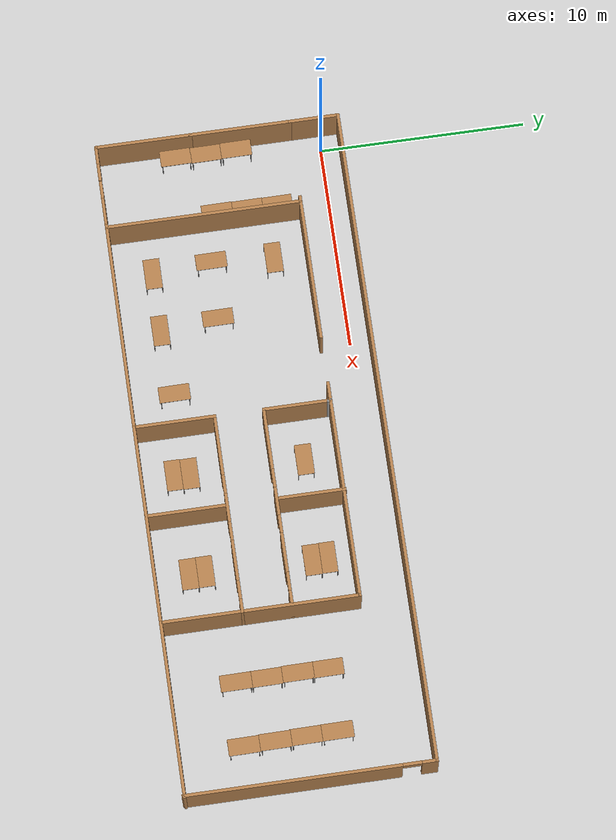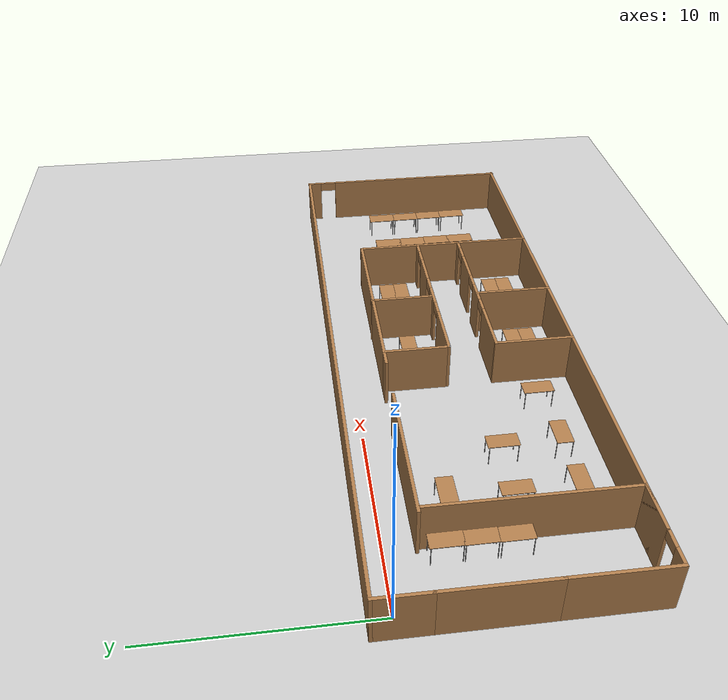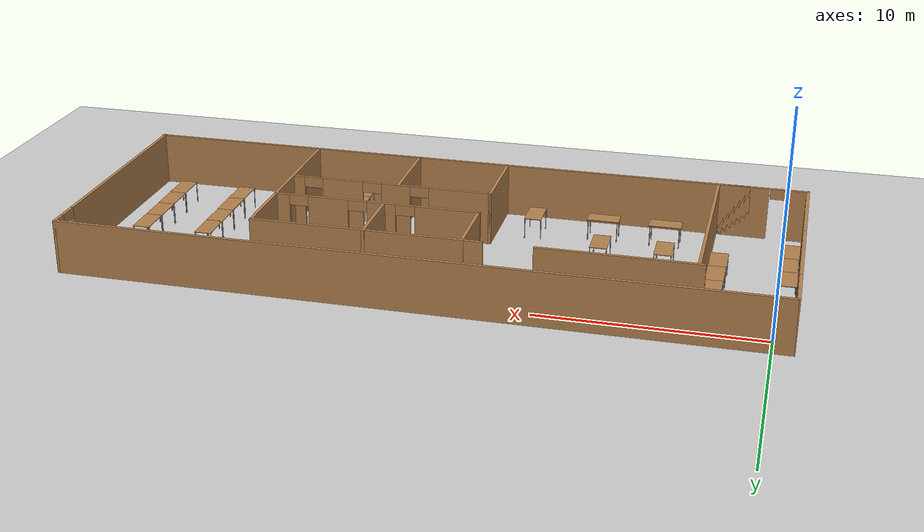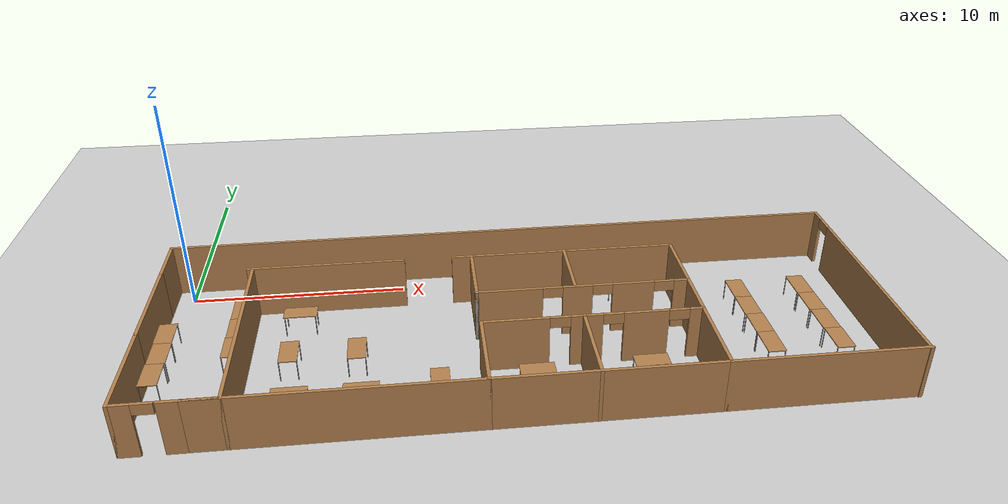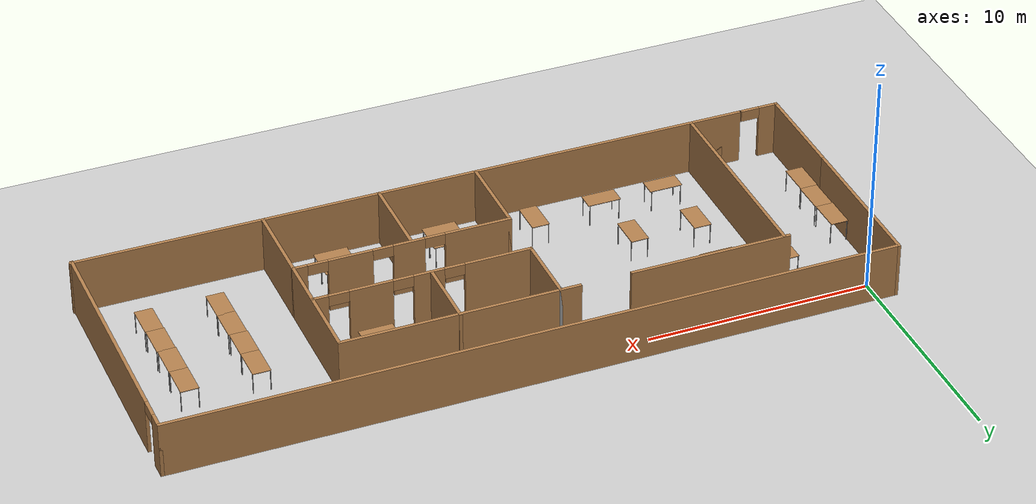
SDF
<sdf version="1.7">
 <world name="default">
  <light name="sun" type="directional">
   <pose>0 0 10 0 -0 0</pose>
   <diffuse>0.8 0.8 0.8 1</diffuse>
   <specular>0.2 0.2 0.2 1</specular>
   <attenuation>
    <range>1000</range>
    <constant>0.9</constant>
    <linear>0.01</linear>
    <quadratic>0.001</quadratic>
   </attenuation>
   <direction>-0.5 0.1 -0.9</direction>
   <spot><inner_angle>0</inner_angle><outer_angle>0</outer_angle><falloff>0</falloff></spot>
  </light>
  <model name="ground_plane">
   <static>1</static>
   <link name="link">
    <collision name="collision">
     <geometry><plane><normal>0 0 1</normal><size>100 100</size></plane></geometry>
     <surface><friction><ode><mu>100</mu><mu2>50</mu2></ode></friction></surface>
    </collision>
    <visual name="visual">
     <cast_shadows>0</cast_shadows>
     <geometry><plane><normal>0 0 1</normal><size>100 100</size></plane></geometry>
     <material>
      <script><uri>file://media/materials/scripts/gazebo.material</uri><name>Gazebo/Grey</name></script>
     </material>
    </visual>
   </link>
  </model>
  <gravity>0 0 -9.8</gravity>
  <magnetic_field>6e-06 2.3e-05 -4.2e-05</magnetic_field>
  <atmosphere type="adiabatic"/>
  <physics type="ode">
   <max_step_size>0.001</max_step_size>
   <real_time_factor>1</real_time_factor>
   <real_time_update_rate>1000</real_time_update_rate>
  </physics>
  <scene><ambient>0.4 0.4 0.4 1</ambient><background>0.7 0.7 0.7 1</background><shadows>1</shadows></scene>
  <audio><device>default</device></audio>
  <spherical_coordinates>
   <surface_model>EARTH_WGS84</surface_model>
   <latitude_deg>0</latitude_deg>
   <longitude_deg>0</longitude_deg>
   <elevation>0</elevation>
   <heading_deg>0</heading_deg>
  </spherical_coordinates>
  <model name="restaurant">
   <pose>15.2138 -4.96934 0 0 -0 0</pose>
   <link name="Wall_100">
    <collision name="Wall_100_Collision">
     <geometry><box><size>32.25 0.15 2.5</size></box></geometry>
     <pose>0 0 1.25 0 -0 0</pose>
    </collision>
    <visual name="Wall_100_Visual">
     <pose>0 0 1.25 0 -0 0</pose>
     <geometry><box><size>32.25 0.15 2.5</size></box></geometry>
     <material>
      <script><uri>file://media/materials/scripts/gazebo.material</uri><name>Gazebo/Wood</name></script>
      <ambient>1 1 1 1</ambient>
     </material>
     <meta><layer>0</layer></meta>
    </visual>
    <pose>-0.024999 5.925 0 0 -0 0</pose>
   </link>
   <link name="Wall_101">
    <pose>16.025 -0 0 0 -0 -1.5708</pose>
    <visual name="Wall_101_Visual_0">
     <pose>-5.61096 0 1.25 0 -0 0</pose>
     <geometry><box><size>0.77808 0.15 2.5</size></box></geometry>
     <material>
      <script><uri>file://media/materials/scripts/gazebo.material</uri><name>Gazebo/Wood</name></script>
      <ambient>1 1 1 1</ambient>
     </material>
     <meta><layer>0</layer></meta>
    </visual>
    <collision name="Wall_101_Collision_0">
     <geometry><box><size>0.77808 0.15 2.5</size></box></geometry>
     <pose>-5.61096 0 1.25 0 -0 0</pose>
    </collision>
    <visual name="Wall_101_Visual_1">
     <pose>0.83904 0 1.25 0 -0 0</pose>
     <geometry><box><size>10.3219 0.15 2.5</size></box></geometry>
     <material>
      <script><uri>file://media/materials/scripts/gazebo.material</uri><name>Gazebo/Wood</name></script>
      <ambient>1 1 1 1</ambient>
     </material>
     <meta><layer>0</layer></meta>
    </visual>
    <collision name="Wall_101_Collision_1">
     <geometry><box><size>10.3219 0.15 2.5</size></box></geometry>
     <pose>0.83904 0 1.25 0 -0 0</pose>
    </collision>
    <visual name="Wall_101_Visual_2">
     <pose>-4.77192 0 2.25 0 -0 0</pose>
     <geometry><box><size>0.9 0.15 0.5</size></box></geometry>
     <material>
      <script><uri>file://media/materials/scripts/gazebo.material</uri><name>Gazebo/Wood</name></script>
      <ambient>1 1 1 1</ambient>
     </material>
     <meta><layer>0</layer></meta>
    </visual>
    <collision name="Wall_101_Collision_2">
     <geometry><box><size>0.9 0.15 0.5</size></box></geometry>
     <pose>-4.77192 0 2.25 0 -0 0</pose>
    </collision>
   </link>
   <link name="Wall_17">
    <collision name="Wall_17_Collision">
     <geometry><box><size>2.5 0.15 2.5</size></box></geometry>
     <pose>0 0 1.25 0 -0 0</pose>
    </collision>
    <visual name="Wall_17_Visual">
     <pose>0 0 1.25 0 -0 0</pose>
     <geometry><box><size>2.5 0.15 2.5</size></box></geometry>
     <material>
      <script><uri>file://media/materials/scripts/gazebo.material</uri><name>Gazebo/Wood</name></script>
      <ambient>1 1 1 1</ambient>
     </material>
     <meta><layer>0</layer></meta>
    </visual>
    <pose>-16.075 4.75 0 0 -0 -1.5708</pose>
   </link>
   <link name="Wall_23">
    <collision name="Wall_23_Collision">
     <geometry><box><size>5 0.15 2.5</size></box></geometry>
     <pose>0 0 1.25 0 -0 0</pose>
    </collision>
    <visual name="Wall_23_Visual">
     <pose>0 0 1.25 0 -0 0</pose>
     <geometry><box><size>5 0.15 2.5</size></box></geometry>
     <material>
      <script><uri>file://media/materials/scripts/gazebo.material</uri><name>Gazebo/Wood</name></script>
      <ambient>1 1 1 1</ambient>
     </material>
     <meta><layer>0</layer></meta>
    </visual>
    <pose>-16.075 1.15 0 0 -0 -1.5708</pose>
   </link>
   <link name="Wall_25">
    <collision name="Wall_25_Collision">
     <geometry><box><size>4.75 0.15 2.5</size></box></geometry>
     <pose>0 0 1.25 0 -0 0</pose>
    </collision>
    <visual name="Wall_25_Visual">
     <pose>0 0 1.25 0 -0 0</pose>
     <geometry><box><size>4.75 0.15 2.5</size></box></geometry>
     <material>
      <script><uri>file://media/materials/scripts/gazebo.material</uri><name>Gazebo/Wood</name></script>
      <ambient>1 1 1 1</ambient>
     </material>
     <meta><layer>0</layer></meta>
    </visual>
    <pose>-16.075 -3.575 0 0 -0 -1.5708</pose>
   </link>
   <link name="Wall_27">
    <pose>-14.025 -5.875 0 0 -0 0</pose>
    <visual name="Wall_27_Visual_0">
     <pose>-1.66236 0 1.25 0 -0 0</pose>
     <geometry><box><size>0.925291 0.15 2.5</size></box></geometry>
     <material>
      <script><uri>file://media/materials/scripts/gazebo.material</uri><name>Gazebo/Wood</name></script>
      <ambient>1 1 1 1</ambient>
     </material>
     <meta><layer>0</layer></meta>
    </visual>
    <collision name="Wall_27_Collision_0">
     <geometry><box><size>0.925291 0.15 2.5</size></box></geometry>
     <pose>-1.66236 0 1.25 0 -0 0</pose>
    </collision>
    <visual name="Wall_27_Visual_1">
     <pose>0.912645 0 1.25 0 -0 0</pose>
     <geometry><box><size>2.42471 0.15 2.5</size></box></geometry>
     <material>
      <script><uri>file://media/materials/scripts/gazebo.material</uri><name>Gazebo/Wood</name></script>
      <ambient>1 1 1 1</ambient>
     </material>
     <meta><layer>0</layer></meta>
    </visual>
    <collision name="Wall_27_Collision_1">
     <geometry><box><size>2.42471 0.15 2.5</size></box></geometry>
     <pose>0.912645 0 1.25 0 -0 0</pose>
    </collision>
    <visual name="Wall_27_Visual_2">
     <pose>1.33783 0 1.25 0 -0 0</pose>
     <geometry><box><size>1.57435 0.15 2.5</size></box></geometry>
     <material>
      <script><uri>file://media/materials/scripts/gazebo.material</uri><name>Gazebo/Wood</name></script>
      <ambient>1 1 1 1</ambient>
     </material>
     <meta><layer>0</layer></meta>
    </visual>
    <collision name="Wall_27_Collision_2">
     <geometry><box><size>1.57435 0.15 2.5</size></box></geometry>
     <pose>1.33783 0 1.25 0 -0 0</pose>
    </collision>
    <visual name="Wall_27_Visual_3">
     <pose>-0.774528 0 2.25 0 -0 0</pose>
     <geometry><box><size>0.850362 0.15 0.5</size></box></geometry>
     <material>
      <script><uri>file://media/materials/scripts/gazebo.material</uri><name>Gazebo/Wood</name></script>
      <ambient>1 1 1 1</ambient>
     </material>
     <meta><layer>0</layer></meta>
    </visual>
    <collision name="Wall_27_Collision_3">
     <geometry><box><size>0.850362 0.15 0.5</size></box></geometry>
     <pose>-0.774528 0 2.25 0 -0 0</pose>
    </collision>
   </link>
   <link name="Wall_28">
    <collision name="Wall_28_Collision">
     <geometry><box><size>9.5 0.15 2.5</size></box></geometry>
     <pose>0 0 1.25 0 -0 0</pose>
    </collision>
    <visual name="Wall_28_Visual">
     <pose>0 0 1.25 0 -0 0</pose>
     <geometry><box><size>9.5 0.15 2.5</size></box></geometry>
     <material>
      <script><uri>file://media/materials/scripts/gazebo.material</uri><name>Gazebo/Wood</name></script>
      <ambient>1 1 1 1</ambient>
     </material>
     <meta><layer>0</layer></meta>
    </visual>
    <pose>-11.975 -1.2 0 0 -0 1.5708</pose>
   </link>
   <link name="Wall_30">
    <collision name="Wall_30_Collision">
     <geometry><box><size>10.25 0.15 2.5</size></box></geometry>
     <pose>0 0 1.25 0 -0 0</pose>
    </collision>
    <visual name="Wall_30_Visual">
     <pose>0 0 1.25 0 -0 0</pose>
     <geometry><box><size>10.25 0.15 2.5</size></box></geometry>
     <material>
      <script><uri>file://media/materials/scripts/gazebo.material</uri><name>Gazebo/Wood</name></script>
      <ambient>1 1 1 1</ambient>
     </material>
     <meta><layer>0</layer></meta>
    </visual>
    <pose>-6.925 -5.875 0 0 -0 0</pose>
   </link>
   <link name="Wall_31">
    <collision name="Wall_31_Collision">
     <geometry><box><size>4 0.15 2.5</size></box></geometry>
     <pose>0 0 1.25 0 -0 0</pose>
    </collision>
    <visual name="Wall_31_Visual">
     <pose>0 0 1.25 0 -0 0</pose>
     <geometry><box><size>4 0.15 2.5</size></box></geometry>
     <material>
      <script><uri>file://media/materials/scripts/gazebo.material</uri><name>Gazebo/Wood</name></script>
      <ambient>1 1 1 1</ambient>
     </material>
     <meta><layer>0</layer></meta>
    </visual>
    <pose>-1.875 -3.95 0 0 -0 1.5708</pose>
   </link>
   <link name="Wall_33">
    <collision name="Wall_33_Collision">
     <geometry><box><size>0.15 0.15 2.5</size></box></geometry>
     <pose>0 0 1.25 0 -0 0</pose>
    </collision>
    <visual name="Wall_33_Visual">
     <pose>0 0 1.25 0 -0 0</pose>
     <geometry><box><size>0.15 0.15 2.5</size></box></geometry>
     <material>
      <script><uri>file://media/materials/scripts/gazebo.material</uri><name>Gazebo/Grey</name></script>
      <ambient>1 1 1 1</ambient>
     </material>
     <meta><layer>0</layer></meta>
    </visual>
    <pose>-1.875 0.325 0 0 -0 0</pose>
   </link>
   <link name="Wall_34">
    <collision name="Wall_34_Collision">
     <geometry><box><size>3.25 0.15 2.5</size></box></geometry>
     <pose>0 0 1.25 0 -0 0</pose>
    </collision>
    <visual name="Wall_34_Visual">
     <pose>0 0 1.25 0 -0 0</pose>
     <geometry><box><size>3.25 0.15 2.5</size></box></geometry>
     <material>
      <script><uri>file://media/materials/scripts/gazebo.material</uri><name>Gazebo/Wood</name></script>
      <ambient>1 1 1 1</ambient>
     </material>
     <meta><layer>0</layer></meta>
    </visual>
    <pose>-1.875 1.875 0 0 -0 1.5708</pose>
   </link>
   <link name="Wall_35">
    <collision name="Wall_35_Collision">
     <geometry><box><size>0.25 0.15 2.5</size></box></geometry>
     <pose>0 0 1.25 0 -0 0</pose>
    </collision>
    <visual name="Wall_35_Visual">
     <pose>0 0 1.25 0 -0 0</pose>
     <geometry><box><size>0.25 0.15 2.5</size></box></geometry>
     <material>
      <script><uri>file://media/materials/scripts/gazebo.material</uri><name>Gazebo/Grey</name></script>
      <ambient>1 1 1 1</ambient>
     </material>
     <meta><layer>0</layer></meta>
    </visual>
    <pose>-1.875 3.475 0 0 -0 1.5708</pose>
   </link>
   <link name="Wall_36">
    <collision name="Wall_36_Collision">
     <geometry><box><size>1 0.15 2.5</size></box></geometry>
     <pose>0 0 1.25 0 -0 0</pose>
    </collision>
    <visual name="Wall_36_Visual">
     <pose>0 0 1.25 0 -0 0</pose>
     <geometry><box><size>1 0.15 2.5</size></box></geometry>
     <material>
      <script><uri>file://media/materials/scripts/gazebo.material</uri><name>Gazebo/Wood</name></script>
      <ambient>1 1 1 1</ambient>
     </material>
     <meta><layer>0</layer></meta>
    </visual>
    <pose>-2.3 3.525 0 0 -0 3.14159</pose>
   </link>
   <link name="Wall_41">
    <collision name="Wall_41_Collision">
     <geometry><box><size>7.25 0.15 2.5</size></box></geometry>
     <pose>0 0 1.25 0 -0 0</pose>
    </collision>
    <visual name="Wall_41_Visual">
     <pose>0 0 1.25 0 -0 0</pose>
     <geometry><box><size>7.25 0.15 2.5</size></box></geometry>
     <material>
      <script><uri>file://media/materials/scripts/gazebo.material</uri><name>Gazebo/Wood</name></script>
      <ambient>1 1 1 1</ambient>
     </material>
     <meta><layer>0</layer></meta>
    </visual>
    <pose>-8.625 3.525 0 0 -0 3.14159</pose>
   </link>
   <link name="Wall_82">
    <collision name="Wall_82_Collision">
     <geometry><box><size>9.75 0.15 2.5</size></box></geometry>
     <pose>0 0 1.25 0 -0 0</pose>
    </collision>
    <visual name="Wall_82_Visual">
     <pose>0 0 1.25 0 -0 0</pose>
     <geometry><box><size>9.75 0.15 2.5</size></box></geometry>
     <material>
      <script><uri>file://media/materials/scripts/gazebo.material</uri><name>Gazebo/Wood</name></script>
      <ambient>1 1 1 1</ambient>
     </material>
     <meta><layer>0</layer></meta>
    </visual>
    <pose>2.925 -5.875 0 0 -0 0</pose>
   </link>
   <link name="Wall_84">
    <collision name="Wall_84_Collision">
     <geometry><box><size>9.75 0.15 2.5</size></box></geometry>
     <pose>0 0 1.25 0 -0 0</pose>
    </collision>
    <visual name="Wall_84_Visual">
     <pose>0 0 1.25 0 -0 0</pose>
     <geometry><box><size>9.75 0.15 2.5</size></box></geometry>
     <material>
      <script><uri>file://media/materials/scripts/gazebo.material</uri><name>Gazebo/Wood</name></script>
      <ambient>1 1 1 1</ambient>
     </material>
     <meta><layer>0</layer></meta>
    </visual>
    <pose>2.925 3.525 0 0 -0 0</pose>
   </link>
   <link name="Wall_85">
    <collision name="Wall_85_Collision">
     <geometry><box><size>9.55 0.15 2.5</size></box></geometry>
     <pose>0 0 1.25 0 -0 0</pose>
    </collision>
    <visual name="Wall_85_Visual">
     <pose>0 0 1.25 0 -0 0</pose>
     <geometry><box><size>9.55 0.15 2.5</size></box></geometry>
     <material>
      <script><uri>file://media/materials/scripts/gazebo.material</uri><name>Gazebo/Wood</name></script>
      <ambient>1 1 1 1</ambient>
     </material>
     <meta><layer>0</layer></meta>
    </visual>
    <pose>7.725 -1.175 0 0 -0 -1.5708</pose>
   </link>
   <link name="Wall_87">
    <pose>2.925 0.325 0 0 -0 0</pose>
    <visual name="Wall_87_Visual_0">
     <pose>-3.36026 0 1.25 0 -0 0</pose>
     <geometry><box><size>3.02949 0.15 2.5</size></box></geometry>
     <material>
      <script><uri>file://media/materials/scripts/gazebo.material</uri><name>Gazebo/Wood</name></script>
      <ambient>1 1 1 1</ambient>
     </material>
     <meta><layer>0</layer></meta>
    </visual>
    <collision name="Wall_87_Collision_0">
     <geometry><box><size>3.02949 0.15 2.5</size></box></geometry>
     <pose>-3.36026 0 1.25 0 -0 0</pose>
    </collision>
    <visual name="Wall_87_Visual_1">
     <pose>-0.26582 0 1.25 0 -0 0</pose>
     <geometry><box><size>1.35939 0.15 2.5</size></box></geometry>
     <material>
      <script><uri>file://media/materials/scripts/gazebo.material</uri><name>Gazebo/Wood</name></script>
      <ambient>1 1 1 1</ambient>
     </material>
     <meta><layer>0</layer></meta>
    </visual>
    <collision name="Wall_87_Collision_1">
     <geometry><box><size>1.35939 0.15 2.5</size></box></geometry>
     <pose>-0.26582 0 1.25 0 -0 0</pose>
    </collision>
    <visual name="Wall_87_Visual_2">
     <pose>2.2689 0 1.25 0 -0 0</pose>
     <geometry><box><size>1.91004 0.15 2.5</size></box></geometry>
     <material>
      <script><uri>file://media/materials/scripts/gazebo.material</uri><name>Gazebo/Wood</name></script>
      <ambient>1 1 1 1</ambient>
     </material>
     <meta><layer>0</layer></meta>
    </visual>
    <collision name="Wall_87_Collision_2">
     <geometry><box><size>1.91004 0.15 2.5</size></box></geometry>
     <pose>2.2689 0 1.25 0 -0 0</pose>
    </collision>
    <visual name="Wall_87_Visual_3">
     <pose>4.49946 0 1.25 0 -0 0</pose>
     <geometry><box><size>0.751084 0.15 2.5</size></box></geometry>
     <material>
      <script><uri>file://media/materials/scripts/gazebo.material</uri><name>Gazebo/Wood</name></script>
      <ambient>1 1 1 1</ambient>
     </material>
     <meta><layer>0</layer></meta>
    </visual>
    <collision name="Wall_87_Collision_3">
     <geometry><box><size>0.751084 0.15 2.5</size></box></geometry>
     <pose>4.49946 0 1.25 0 -0 0</pose>
    </collision>
    <visual name="Wall_87_Visual_4">
     <pose>-1.39551 0 2.25 0 -0 0</pose>
     <geometry><box><size>0.9 0.15 0.5</size></box></geometry>
     <material>
      <script><uri>file://media/materials/scripts/gazebo.material</uri><name>Gazebo/Wood</name></script>
      <ambient>1 1 1 1</ambient>
     </material>
     <meta><layer>0</layer></meta>
    </visual>
    <collision name="Wall_87_Collision_4">
     <geometry><box><size>0.9 0.15 0.5</size></box></geometry>
     <pose>-1.39551 0 2.25 0 -0 0</pose>
    </collision>
    <visual name="Wall_87_Visual_5">
     <pose>0.863874 0 2.25 0 -0 0</pose>
     <geometry><box><size>0.9 0.15 0.5</size></box></geometry>
     <material>
      <script><uri>file://media/materials/scripts/gazebo.material</uri><name>Gazebo/Wood</name></script>
      <ambient>1 1 1 1</ambient>
     </material>
     <meta><layer>0</layer></meta>
    </visual>
    <collision name="Wall_87_Collision_5">
     <geometry><box><size>0.9 0.15 0.5</size></box></geometry>
     <pose>0.863874 0 2.25 0 -0 0</pose>
    </collision>
    <visual name="Wall_87_Visual_6">
     <pose>3.67392 0 2.25 0 -0 0</pose>
     <geometry><box><size>0.9 0.15 0.5</size></box></geometry>
     <material>
      <script><uri>file://media/materials/scripts/gazebo.material</uri><name>Gazebo/Wood</name></script>
      <ambient>1 1 1 1</ambient>
     </material>
     <meta><layer>0</layer></meta>
    </visual>
    <collision name="Wall_87_Collision_6">
     <geometry><box><size>0.9 0.15 0.5</size></box></geometry>
     <pose>3.67392 0 2.25 0 -0 0</pose>
    </collision>
   </link>
   <link name="Wall_89">
    <pose>2.925 -2.025 0 0 -0 0</pose>
    <visual name="Wall_89_Visual_0">
     <pose>-3.37861 0 1.25 0 -0 0</pose>
     <geometry><box><size>2.99277 0.15 2.5</size></box></geometry>
     <material>
      <script><uri>file://media/materials/scripts/gazebo.material</uri><name>Gazebo/Wood</name></script>
      <ambient>1 1 1 1</ambient>
     </material>
     <meta><layer>0</layer></meta>
    </visual>
    <collision name="Wall_89_Collision_0">
     <geometry><box><size>2.99277 0.15 2.5</size></box></geometry>
     <pose>-3.37861 0 1.25 0 -0 0</pose>
    </collision>
    <visual name="Wall_89_Visual_1">
     <pose>-0.278618 0 1.25 0 -0 0</pose>
     <geometry><box><size>1.40722 0.15 2.5</size></box></geometry>
     <material>
      <script><uri>file://media/materials/scripts/gazebo.material</uri><name>Gazebo/Wood</name></script>
      <ambient>1 1 1 1</ambient>
     </material>
     <meta><layer>0</layer></meta>
    </visual>
    <collision name="Wall_89_Collision_1">
     <geometry><box><size>1.40722 0.15 2.5</size></box></geometry>
     <pose>-0.278618 0 1.25 0 -0 0</pose>
    </collision>
    <visual name="Wall_89_Visual_2">
     <pose>2.31228 0 1.25 0 -0 0</pose>
     <geometry><box><size>1.97457 0.15 2.5</size></box></geometry>
     <material>
      <script><uri>file://media/materials/scripts/gazebo.material</uri><name>Gazebo/Wood</name></script>
      <ambient>1 1 1 1</ambient>
     </material>
     <meta><layer>0</layer></meta>
    </visual>
    <collision name="Wall_89_Collision_2">
     <geometry><box><size>1.97457 0.15 2.5</size></box></geometry>
     <pose>2.31228 0 1.25 0 -0 0</pose>
    </collision>
    <visual name="Wall_89_Visual_3">
     <pose>4.53728 0 1.25 0 -0 0</pose>
     <geometry><box><size>0.675437 0.15 2.5</size></box></geometry>
     <material>
      <script><uri>file://media/materials/scripts/gazebo.material</uri><name>Gazebo/Wood</name></script>
      <ambient>1 1 1 1</ambient>
     </material>
     <meta><layer>0</layer></meta>
    </visual>
    <collision name="Wall_89_Collision_3">
     <geometry><box><size>0.675437 0.15 2.5</size></box></geometry>
     <pose>4.53728 0 1.25 0 -0 0</pose>
    </collision>
    <visual name="Wall_89_Visual_4">
     <pose>-1.43223 0 2.25 0 -0 0</pose>
     <geometry><box><size>0.9 0.15 0.5</size></box></geometry>
     <material>
      <script><uri>file://media/materials/scripts/gazebo.material</uri><name>Gazebo/Wood</name></script>
      <ambient>1 1 1 1</ambient>
     </material>
     <meta><layer>0</layer></meta>
    </visual>
    <collision name="Wall_89_Collision_4">
     <geometry><box><size>0.9 0.15 0.5</size></box></geometry>
     <pose>-1.43223 0 2.25 0 -0 0</pose>
    </collision>
    <visual name="Wall_89_Visual_5">
     <pose>0.874992 0 2.25 0 -0 0</pose>
     <geometry><box><size>0.9 0.15 0.5</size></box></geometry>
     <material>
      <script><uri>file://media/materials/scripts/gazebo.material</uri><name>Gazebo/Wood</name></script>
      <ambient>1 1 1 1</ambient>
     </material>
     <meta><layer>0</layer></meta>
    </visual>
    <collision name="Wall_89_Collision_5">
     <geometry><box><size>0.9 0.15 0.5</size></box></geometry>
     <pose>0.874992 0 2.25 0 -0 0</pose>
    </collision>
    <visual name="Wall_89_Visual_6">
     <pose>3.74956 0 2.25 0 -0 0</pose>
     <geometry><box><size>0.9 0.15 0.5</size></box></geometry>
     <material>
      <script><uri>file://media/materials/scripts/gazebo.material</uri><name>Gazebo/Wood</name></script>
      <ambient>1 1 1 1</ambient>
     </material>
     <meta><layer>0</layer></meta>
    </visual>
    <collision name="Wall_89_Collision_6">
     <geometry><box><size>0.9 0.15 0.5</size></box></geometry>
     <pose>3.74956 0 2.25 0 -0 0</pose>
    </collision>
   </link>
   <link name="Wall_94">
    <collision name="Wall_94_Collision">
     <geometry><box><size>3.25 0.15 2.5</size></box></geometry>
     <pose>0 0 1.25 0 -0 0</pose>
    </collision>
    <visual name="Wall_94_Visual">
     <pose>0 0 1.25 0 -0 0</pose>
     <geometry><box><size>3.25 0.15 2.5</size></box></geometry>
     <material>
      <script><uri>file://media/materials/scripts/gazebo.material</uri><name>Gazebo/Wood</name></script>
      <ambient>1 1 1 1</ambient>
     </material>
     <meta><layer>0</layer></meta>
    </visual>
    <pose>2.54208 2.01323 0 0 -0 -1.5708</pose>
   </link>
   <link name="Wall_96">
    <collision name="Wall_96_Collision">
     <geometry><box><size>4 0.15 2.5</size></box></geometry>
     <pose>0 0 1.25 0 -0 0</pose>
    </collision>
    <visual name="Wall_96_Visual">
     <pose>0 0 1.25 0 -0 0</pose>
     <geometry><box><size>4 0.15 2.5</size></box></geometry>
     <material>
      <script><uri>file://media/materials/scripts/gazebo.material</uri><name>Gazebo/Wood</name></script>
      <ambient>1 1 1 1</ambient>
     </material>
     <meta><layer>0</layer></meta>
    </visual>
    <pose>2.5286 -3.95218 0 0 -0 -1.5708</pose>
   </link>
   <link name="Wall_98">
    <collision name="Wall_98_Collision">
     <geometry><box><size>8.5 0.15 2.5</size></box></geometry>
     <pose>0 0 1.25 0 -0 0</pose>
    </collision>
    <visual name="Wall_98_Visual">
     <pose>0 0 1.25 0 -0 0</pose>
     <geometry><box><size>8.5 0.15 2.5</size></box></geometry>
     <material>
      <script><uri>file://media/materials/scripts/gazebo.material</uri><name>Gazebo/Wood</name></script>
      <ambient>1 1 1 1</ambient>
     </material>
     <meta><layer>0</layer></meta>
    </visual>
    <pose>11.9 -5.875 0 0 -0 0</pose>
   </link>
   <static>1</static>
  </model>
  <model name="table">
   <static>1</static>
   <link name="link">
    <collision name="surface">
     <pose>0 0 1 0 -0 0</pose>
     <geometry><box><size>1.5 0.8 0.03</size></box></geometry>
     <surface><friction><ode><mu>0.6</mu><mu2>0.6</mu2></ode></friction></surface>
    </collision>
    <visual name="visual1">
     <pose>0 0 1 0 -0 0</pose>
     <geometry><box><size>1.5 0.8 0.03</size></box></geometry>
     <material>
      <script><uri>file://media/materials/scripts/gazebo.material</uri><name>Gazebo/Wood</name></script>
     </material>
    </visual>
    <collision name="front_left_leg">
     <pose>0.68 0.38 0.5 0 -0 0</pose>
     <geometry><cylinder><radius>0.02</radius><length>1</length></cylinder></geometry>
    </collision>
    <visual name="front_left_leg">
     <pose>0.68 0.38 0.5 0 -0 0</pose>
     <geometry><cylinder><radius>0.02</radius><length>1</length></cylinder></geometry>
     <material>
      <script><uri>file://media/materials/scripts/gazebo.material</uri><name>Gazebo/Grey</name></script>
     </material>
    </visual>
    <collision name="front_right_leg">
     <pose>0.68 -0.38 0.5 0 -0 0</pose>
     <geometry><cylinder><radius>0.02</radius><length>1</length></cylinder></geometry>
    </collision>
    <visual name="front_right_leg">
     <pose>0.68 -0.38 0.5 0 -0 0</pose>
     <geometry><cylinder><radius>0.02</radius><length>1</length></cylinder></geometry>
     <material>
      <script><uri>file://media/materials/scripts/gazebo.material</uri><name>Gazebo/Grey</name></script>
     </material>
    </visual>
    <collision name="back_right_leg">
     <pose>-0.68 -0.38 0.5 0 -0 0</pose>
     <geometry><cylinder><radius>0.02</radius><length>1</length></cylinder></geometry>
    </collision>
    <visual name="back_right_leg">
     <pose>-0.68 -0.38 0.5 0 -0 0</pose>
     <geometry><cylinder><radius>0.02</radius><length>1</length></cylinder></geometry>
     <material>
      <script><uri>file://media/materials/scripts/gazebo.material</uri><name>Gazebo/Grey</name></script>
     </material>
    </visual>
    <collision name="back_left_leg">
     <pose>-0.68 0.38 0.5 0 -0 0</pose>
     <geometry><cylinder><radius>0.02</radius><length>1</length></cylinder></geometry>
    </collision>
    <visual name="back_left_leg">
     <pose>-0.68 0.38 0.5 0 -0 0</pose>
     <geometry><cylinder><radius>0.02</radius><length>1</length></cylinder></geometry>
     <material>
      <script><uri>file://media/materials/scripts/gazebo.material</uri><name>Gazebo/Grey</name></script>
     </material>
    </visual>
   </link>
   <pose>28.9002 -3.35359 0 0 0 -1.56386</pose>
  </model>
  <model name="table_clone">
   <static>1</static>
   <link name="link">
    <collision name="surface">
     <pose>0 0 1 0 -0 0</pose>
     <geometry><box><size>1.5 0.8 0.03</size></box></geometry>
     <surface><friction><ode><mu>0.6</mu><mu2>0.6</mu2></ode></friction></surface>
    </collision>
    <visual name="visual1">
     <pose>0 0 1 0 -0 0</pose>
     <geometry><box><size>1.5 0.8 0.03</size></box></geometry>
     <material>
      <script><uri>file://media/materials/scripts/gazebo.material</uri><name>Gazebo/Wood</name></script>
     </material>
    </visual>
    <collision name="front_left_leg">
     <pose>0.68 0.38 0.5 0 -0 0</pose>
     <geometry><cylinder><radius>0.02</radius><length>1</length></cylinder></geometry>
    </collision>
    <visual name="front_left_leg">
     <pose>0.68 0.38 0.5 0 -0 0</pose>
     <geometry><cylinder><radius>0.02</radius><length>1</length></cylinder></geometry>
     <material>
      <script><uri>file://media/materials/scripts/gazebo.material</uri><name>Gazebo/Grey</name></script>
     </material>
    </visual>
    <collision name="front_right_leg">
     <pose>0.68 -0.38 0.5 0 -0 0</pose>
     <geometry><cylinder><radius>0.02</radius><length>1</length></cylinder></geometry>
    </collision>
    <visual name="front_right_leg">
     <pose>0.68 -0.38 0.5 0 -0 0</pose>
     <geometry><cylinder><radius>0.02</radius><length>1</length></cylinder></geometry>
     <material>
      <script><uri>file://media/materials/scripts/gazebo.material</uri><name>Gazebo/Grey</name></script>
     </material>
    </visual>
    <collision name="back_right_leg">
     <pose>-0.68 -0.38 0.5 0 -0 0</pose>
     <geometry><cylinder><radius>0.02</radius><length>1</length></cylinder></geometry>
    </collision>
    <visual name="back_right_leg">
     <pose>-0.68 -0.38 0.5 0 -0 0</pose>
     <geometry><cylinder><radius>0.02</radius><length>1</length></cylinder></geometry>
     <material>
      <script><uri>file://media/materials/scripts/gazebo.material</uri><name>Gazebo/Grey</name></script>
     </material>
    </visual>
    <collision name="back_left_leg">
     <pose>-0.68 0.38 0.5 0 -0 0</pose>
     <geometry><cylinder><radius>0.02</radius><length>1</length></cylinder></geometry>
    </collision>
    <visual name="back_left_leg">
     <pose>-0.68 0.38 0.5 0 -0 0</pose>
     <geometry><cylinder><radius>0.02</radius><length>1</length></cylinder></geometry>
     <material>
      <script><uri>file://media/materials/scripts/gazebo.material</uri><name>Gazebo/Grey</name></script>
     </material>
    </visual>
   </link>
   <pose>28.9188 -4.82907 0 0 0 -1.56386</pose>
  </model>
  <model name="table_clone_0">
   <static>1</static>
   <link name="link">
    <collision name="surface">
     <pose>0 0 1 0 -0 0</pose>
     <geometry><box><size>1.5 0.8 0.03</size></box></geometry>
     <surface><friction><ode><mu>0.6</mu><mu2>0.6</mu2></ode></friction></surface>
    </collision>
    <visual name="visual1">
     <pose>0 0 1 0 -0 0</pose>
     <geometry><box><size>1.5 0.8 0.03</size></box></geometry>
     <material>
      <script><uri>file://media/materials/scripts/gazebo.material</uri><name>Gazebo/Wood</name></script>
     </material>
    </visual>
    <collision name="front_left_leg">
     <pose>0.68 0.38 0.5 0 -0 0</pose>
     <geometry><cylinder><radius>0.02</radius><length>1</length></cylinder></geometry>
    </collision>
    <visual name="front_left_leg">
     <pose>0.68 0.38 0.5 0 -0 0</pose>
     <geometry><cylinder><radius>0.02</radius><length>1</length></cylinder></geometry>
     <material>
      <script><uri>file://media/materials/scripts/gazebo.material</uri><name>Gazebo/Grey</name></script>
     </material>
    </visual>
    <collision name="front_right_leg">
     <pose>0.68 -0.38 0.5 0 -0 0</pose>
     <geometry><cylinder><radius>0.02</radius><length>1</length></cylinder></geometry>
    </collision>
    <visual name="front_right_leg">
     <pose>0.68 -0.38 0.5 0 -0 0</pose>
     <geometry><cylinder><radius>0.02</radius><length>1</length></cylinder></geometry>
     <material>
      <script><uri>file://media/materials/scripts/gazebo.material</uri><name>Gazebo/Grey</name></script>
     </material>
    </visual>
    <collision name="back_right_leg">
     <pose>-0.68 -0.38 0.5 0 -0 0</pose>
     <geometry><cylinder><radius>0.02</radius><length>1</length></cylinder></geometry>
    </collision>
    <visual name="back_right_leg">
     <pose>-0.68 -0.38 0.5 0 -0 0</pose>
     <geometry><cylinder><radius>0.02</radius><length>1</length></cylinder></geometry>
     <material>
      <script><uri>file://media/materials/scripts/gazebo.material</uri><name>Gazebo/Grey</name></script>
     </material>
    </visual>
    <collision name="back_left_leg">
     <pose>-0.68 0.38 0.5 0 -0 0</pose>
     <geometry><cylinder><radius>0.02</radius><length>1</length></cylinder></geometry>
    </collision>
    <visual name="back_left_leg">
     <pose>-0.68 0.38 0.5 0 -0 0</pose>
     <geometry><cylinder><radius>0.02</radius><length>1</length></cylinder></geometry>
     <material>
      <script><uri>file://media/materials/scripts/gazebo.material</uri><name>Gazebo/Grey</name></script>
     </material>
    </visual>
   </link>
   <pose>28.9534 -6.29686 0 0 0 -1.56386</pose>
  </model>
  <model name="table_clone_1">
   <static>1</static>
   <link name="link">
    <collision name="surface">
     <pose>0 0 1 0 -0 0</pose>
     <geometry><box><size>1.5 0.8 0.03</size></box></geometry>
     <surface><friction><ode><mu>0.6</mu><mu2>0.6</mu2></ode></friction></surface>
    </collision>
    <visual name="visual1">
     <pose>0 0 1 0 -0 0</pose>
     <geometry><box><size>1.5 0.8 0.03</size></box></geometry>
     <material>
      <script><uri>file://media/materials/scripts/gazebo.material</uri><name>Gazebo/Wood</name></script>
     </material>
    </visual>
    <collision name="front_left_leg">
     <pose>0.68 0.38 0.5 0 -0 0</pose>
     <geometry><cylinder><radius>0.02</radius><length>1</length></cylinder></geometry>
    </collision>
    <visual name="front_left_leg">
     <pose>0.68 0.38 0.5 0 -0 0</pose>
     <geometry><cylinder><radius>0.02</radius><length>1</length></cylinder></geometry>
     <material>
      <script><uri>file://media/materials/scripts/gazebo.material</uri><name>Gazebo/Grey</name></script>
     </material>
    </visual>
    <collision name="front_right_leg">
     <pose>0.68 -0.38 0.5 0 -0 0</pose>
     <geometry><cylinder><radius>0.02</radius><length>1</length></cylinder></geometry>
    </collision>
    <visual name="front_right_leg">
     <pose>0.68 -0.38 0.5 0 -0 0</pose>
     <geometry><cylinder><radius>0.02</radius><length>1</length></cylinder></geometry>
     <material>
      <script><uri>file://media/materials/scripts/gazebo.material</uri><name>Gazebo/Grey</name></script>
     </material>
    </visual>
    <collision name="back_right_leg">
     <pose>-0.68 -0.38 0.5 0 -0 0</pose>
     <geometry><cylinder><radius>0.02</radius><length>1</length></cylinder></geometry>
    </collision>
    <visual name="back_right_leg">
     <pose>-0.68 -0.38 0.5 0 -0 0</pose>
     <geometry><cylinder><radius>0.02</radius><length>1</length></cylinder></geometry>
     <material>
      <script><uri>file://media/materials/scripts/gazebo.material</uri><name>Gazebo/Grey</name></script>
     </material>
    </visual>
    <collision name="back_left_leg">
     <pose>-0.68 0.38 0.5 0 -0 0</pose>
     <geometry><cylinder><radius>0.02</radius><length>1</length></cylinder></geometry>
    </collision>
    <visual name="back_left_leg">
     <pose>-0.68 0.38 0.5 0 -0 0</pose>
     <geometry><cylinder><radius>0.02</radius><length>1</length></cylinder></geometry>
     <material>
      <script><uri>file://media/materials/scripts/gazebo.material</uri><name>Gazebo/Grey</name></script>
     </material>
    </visual>
   </link>
   <pose>28.9886 -7.78775 0 0 0 -1.56386</pose>
  </model>
  <model name="table_clone_2">
   <static>1</static>
   <link name="link">
    <collision name="surface">
     <pose>0 0 1 0 -0 0</pose>
     <geometry><box><size>1.5 0.8 0.03</size></box></geometry>
     <surface><friction><ode><mu>0.6</mu><mu2>0.6</mu2></ode></friction></surface>
    </collision>
    <visual name="visual1">
     <pose>0 0 1 0 -0 0</pose>
     <geometry><box><size>1.5 0.8 0.03</size></box></geometry>
     <material>
      <script><uri>file://media/materials/scripts/gazebo.material</uri><name>Gazebo/Wood</name></script>
     </material>
    </visual>
    <collision name="front_left_leg">
     <pose>0.68 0.38 0.5 0 -0 0</pose>
     <geometry><cylinder><radius>0.02</radius><length>1</length></cylinder></geometry>
    </collision>
    <visual name="front_left_leg">
     <pose>0.68 0.38 0.5 0 -0 0</pose>
     <geometry><cylinder><radius>0.02</radius><length>1</length></cylinder></geometry>
     <material>
      <script><uri>file://media/materials/scripts/gazebo.material</uri><name>Gazebo/Grey</name></script>
     </material>
    </visual>
    <collision name="front_right_leg">
     <pose>0.68 -0.38 0.5 0 -0 0</pose>
     <geometry><cylinder><radius>0.02</radius><length>1</length></cylinder></geometry>
    </collision>
    <visual name="front_right_leg">
     <pose>0.68 -0.38 0.5 0 -0 0</pose>
     <geometry><cylinder><radius>0.02</radius><length>1</length></cylinder></geometry>
     <material>
      <script><uri>file://media/materials/scripts/gazebo.material</uri><name>Gazebo/Grey</name></script>
     </material>
    </visual>
    <collision name="back_right_leg">
     <pose>-0.68 -0.38 0.5 0 -0 0</pose>
     <geometry><cylinder><radius>0.02</radius><length>1</length></cylinder></geometry>
    </collision>
    <visual name="back_right_leg">
     <pose>-0.68 -0.38 0.5 0 -0 0</pose>
     <geometry><cylinder><radius>0.02</radius><length>1</length></cylinder></geometry>
     <material>
      <script><uri>file://media/materials/scripts/gazebo.material</uri><name>Gazebo/Grey</name></script>
     </material>
    </visual>
    <collision name="back_left_leg">
     <pose>-0.68 0.38 0.5 0 -0 0</pose>
     <geometry><cylinder><radius>0.02</radius><length>1</length></cylinder></geometry>
    </collision>
    <visual name="back_left_leg">
     <pose>-0.68 0.38 0.5 0 -0 0</pose>
     <geometry><cylinder><radius>0.02</radius><length>1</length></cylinder></geometry>
     <material>
      <script><uri>file://media/materials/scripts/gazebo.material</uri><name>Gazebo/Grey</name></script>
     </material>
    </visual>
   </link>
   <pose>25.8561 -3.38625 0 0 0 -1.56386</pose>
  </model>
  <model name="table_clone_3">
   <static>1</static>
   <link name="link">
    <collision name="surface">
     <pose>0 0 1 0 -0 0</pose>
     <geometry><box><size>1.5 0.8 0.03</size></box></geometry>
     <surface><friction><ode><mu>0.6</mu><mu2>0.6</mu2></ode></friction></surface>
    </collision>
    <visual name="visual1">
     <pose>0 0 1 0 -0 0</pose>
     <geometry><box><size>1.5 0.8 0.03</size></box></geometry>
     <material>
      <script><uri>file://media/materials/scripts/gazebo.material</uri><name>Gazebo/Wood</name></script>
     </material>
    </visual>
    <collision name="front_left_leg">
     <pose>0.68 0.38 0.5 0 -0 0</pose>
     <geometry><cylinder><radius>0.02</radius><length>1</length></cylinder></geometry>
    </collision>
    <visual name="front_left_leg">
     <pose>0.68 0.38 0.5 0 -0 0</pose>
     <geometry><cylinder><radius>0.02</radius><length>1</length></cylinder></geometry>
     <material>
      <script><uri>file://media/materials/scripts/gazebo.material</uri><name>Gazebo/Grey</name></script>
     </material>
    </visual>
    <collision name="front_right_leg">
     <pose>0.68 -0.38 0.5 0 -0 0</pose>
     <geometry><cylinder><radius>0.02</radius><length>1</length></cylinder></geometry>
    </collision>
    <visual name="front_right_leg">
     <pose>0.68 -0.38 0.5 0 -0 0</pose>
     <geometry><cylinder><radius>0.02</radius><length>1</length></cylinder></geometry>
     <material>
      <script><uri>file://media/materials/scripts/gazebo.material</uri><name>Gazebo/Grey</name></script>
     </material>
    </visual>
    <collision name="back_right_leg">
     <pose>-0.68 -0.38 0.5 0 -0 0</pose>
     <geometry><cylinder><radius>0.02</radius><length>1</length></cylinder></geometry>
    </collision>
    <visual name="back_right_leg">
     <pose>-0.68 -0.38 0.5 0 -0 0</pose>
     <geometry><cylinder><radius>0.02</radius><length>1</length></cylinder></geometry>
     <material>
      <script><uri>file://media/materials/scripts/gazebo.material</uri><name>Gazebo/Grey</name></script>
     </material>
    </visual>
    <collision name="back_left_leg">
     <pose>-0.68 0.38 0.5 0 -0 0</pose>
     <geometry><cylinder><radius>0.02</radius><length>1</length></cylinder></geometry>
    </collision>
    <visual name="back_left_leg">
     <pose>-0.68 0.38 0.5 0 -0 0</pose>
     <geometry><cylinder><radius>0.02</radius><length>1</length></cylinder></geometry>
     <material>
      <script><uri>file://media/materials/scripts/gazebo.material</uri><name>Gazebo/Grey</name></script>
     </material>
    </visual>
   </link>
   <pose>25.8669 -4.80788 0 0 0 -1.56386</pose>
  </model>
  <model name="table_clone_4">
   <static>1</static>
   <link name="link">
    <collision name="surface">
     <pose>0 0 1 0 -0 0</pose>
     <geometry><box><size>1.5 0.8 0.03</size></box></geometry>
     <surface><friction><ode><mu>0.6</mu><mu2>0.6</mu2></ode></friction></surface>
    </collision>
    <visual name="visual1">
     <pose>0 0 1 0 -0 0</pose>
     <geometry><box><size>1.5 0.8 0.03</size></box></geometry>
     <material>
      <script><uri>file://media/materials/scripts/gazebo.material</uri><name>Gazebo/Wood</name></script>
     </material>
    </visual>
    <collision name="front_left_leg">
     <pose>0.68 0.38 0.5 0 -0 0</pose>
     <geometry><cylinder><radius>0.02</radius><length>1</length></cylinder></geometry>
    </collision>
    <visual name="front_left_leg">
     <pose>0.68 0.38 0.5 0 -0 0</pose>
     <geometry><cylinder><radius>0.02</radius><length>1</length></cylinder></geometry>
     <material>
      <script><uri>file://media/materials/scripts/gazebo.material</uri><name>Gazebo/Grey</name></script>
     </material>
    </visual>
    <collision name="front_right_leg">
     <pose>0.68 -0.38 0.5 0 -0 0</pose>
     <geometry><cylinder><radius>0.02</radius><length>1</length></cylinder></geometry>
    </collision>
    <visual name="front_right_leg">
     <pose>0.68 -0.38 0.5 0 -0 0</pose>
     <geometry><cylinder><radius>0.02</radius><length>1</length></cylinder></geometry>
     <material>
      <script><uri>file://media/materials/scripts/gazebo.material</uri><name>Gazebo/Grey</name></script>
     </material>
    </visual>
    <collision name="back_right_leg">
     <pose>-0.68 -0.38 0.5 0 -0 0</pose>
     <geometry><cylinder><radius>0.02</radius><length>1</length></cylinder></geometry>
    </collision>
    <visual name="back_right_leg">
     <pose>-0.68 -0.38 0.5 0 -0 0</pose>
     <geometry><cylinder><radius>0.02</radius><length>1</length></cylinder></geometry>
     <material>
      <script><uri>file://media/materials/scripts/gazebo.material</uri><name>Gazebo/Grey</name></script>
     </material>
    </visual>
    <collision name="back_left_leg">
     <pose>-0.68 0.38 0.5 0 -0 0</pose>
     <geometry><cylinder><radius>0.02</radius><length>1</length></cylinder></geometry>
    </collision>
    <visual name="back_left_leg">
     <pose>-0.68 0.38 0.5 0 -0 0</pose>
     <geometry><cylinder><radius>0.02</radius><length>1</length></cylinder></geometry>
     <material>
      <script><uri>file://media/materials/scripts/gazebo.material</uri><name>Gazebo/Grey</name></script>
     </material>
    </visual>
   </link>
   <pose>25.902 -6.29777 0 0 0 -1.56386</pose>
  </model>
  <model name="table_clone_5">
   <static>1</static>
   <link name="link">
    <collision name="surface">
     <pose>0 0 1 0 -0 0</pose>
     <geometry><box><size>1.5 0.8 0.03</size></box></geometry>
     <surface><friction><ode><mu>0.6</mu><mu2>0.6</mu2></ode></friction></surface>
    </collision>
    <visual name="visual1">
     <pose>0 0 1 0 -0 0</pose>
     <geometry><box><size>1.5 0.8 0.03</size></box></geometry>
     <material>
      <script><uri>file://media/materials/scripts/gazebo.material</uri><name>Gazebo/Wood</name></script>
     </material>
    </visual>
    <collision name="front_left_leg">
     <pose>0.68 0.38 0.5 0 -0 0</pose>
     <geometry><cylinder><radius>0.02</radius><length>1</length></cylinder></geometry>
    </collision>
    <visual name="front_left_leg">
     <pose>0.68 0.38 0.5 0 -0 0</pose>
     <geometry><cylinder><radius>0.02</radius><length>1</length></cylinder></geometry>
     <material>
      <script><uri>file://media/materials/scripts/gazebo.material</uri><name>Gazebo/Grey</name></script>
     </material>
    </visual>
    <collision name="front_right_leg">
     <pose>0.68 -0.38 0.5 0 -0 0</pose>
     <geometry><cylinder><radius>0.02</radius><length>1</length></cylinder></geometry>
    </collision>
    <visual name="front_right_leg">
     <pose>0.68 -0.38 0.5 0 -0 0</pose>
     <geometry><cylinder><radius>0.02</radius><length>1</length></cylinder></geometry>
     <material>
      <script><uri>file://media/materials/scripts/gazebo.material</uri><name>Gazebo/Grey</name></script>
     </material>
    </visual>
    <collision name="back_right_leg">
     <pose>-0.68 -0.38 0.5 0 -0 0</pose>
     <geometry><cylinder><radius>0.02</radius><length>1</length></cylinder></geometry>
    </collision>
    <visual name="back_right_leg">
     <pose>-0.68 -0.38 0.5 0 -0 0</pose>
     <geometry><cylinder><radius>0.02</radius><length>1</length></cylinder></geometry>
     <material>
      <script><uri>file://media/materials/scripts/gazebo.material</uri><name>Gazebo/Grey</name></script>
     </material>
    </visual>
    <collision name="back_left_leg">
     <pose>-0.68 0.38 0.5 0 -0 0</pose>
     <geometry><cylinder><radius>0.02</radius><length>1</length></cylinder></geometry>
    </collision>
    <visual name="back_left_leg">
     <pose>-0.68 0.38 0.5 0 -0 0</pose>
     <geometry><cylinder><radius>0.02</radius><length>1</length></cylinder></geometry>
     <material>
      <script><uri>file://media/materials/scripts/gazebo.material</uri><name>Gazebo/Grey</name></script>
     </material>
    </visual>
   </link>
   <pose>25.9134 -7.74235 0 0 0 -1.56386</pose>
  </model>
  <model name="table_clone_6">
   <static>1</static>
   <link name="link">
    <collision name="surface">
     <pose>0 0 1 0 -0 0</pose>
     <geometry><box><size>1.5 0.8 0.03</size></box></geometry>
     <surface><friction><ode><mu>0.6</mu><mu2>0.6</mu2></ode></friction></surface>
    </collision>
    <visual name="visual1">
     <pose>0 0 1 0 -0 0</pose>
     <geometry><box><size>1.5 0.8 0.03</size></box></geometry>
     <material>
      <script><uri>file://media/materials/scripts/gazebo.material</uri><name>Gazebo/Wood</name></script>
     </material>
    </visual>
    <collision name="front_left_leg">
     <pose>0.68 0.38 0.5 0 -0 0</pose>
     <geometry><cylinder><radius>0.02</radius><length>1</length></cylinder></geometry>
    </collision>
    <visual name="front_left_leg">
     <pose>0.68 0.38 0.5 0 -0 0</pose>
     <geometry><cylinder><radius>0.02</radius><length>1</length></cylinder></geometry>
     <material>
      <script><uri>file://media/materials/scripts/gazebo.material</uri><name>Gazebo/Grey</name></script>
     </material>
    </visual>
    <collision name="front_right_leg">
     <pose>0.68 -0.38 0.5 0 -0 0</pose>
     <geometry><cylinder><radius>0.02</radius><length>1</length></cylinder></geometry>
    </collision>
    <visual name="front_right_leg">
     <pose>0.68 -0.38 0.5 0 -0 0</pose>
     <geometry><cylinder><radius>0.02</radius><length>1</length></cylinder></geometry>
     <material>
      <script><uri>file://media/materials/scripts/gazebo.material</uri><name>Gazebo/Grey</name></script>
     </material>
    </visual>
    <collision name="back_right_leg">
     <pose>-0.68 -0.38 0.5 0 -0 0</pose>
     <geometry><cylinder><radius>0.02</radius><length>1</length></cylinder></geometry>
    </collision>
    <visual name="back_right_leg">
     <pose>-0.68 -0.38 0.5 0 -0 0</pose>
     <geometry><cylinder><radius>0.02</radius><length>1</length></cylinder></geometry>
     <material>
      <script><uri>file://media/materials/scripts/gazebo.material</uri><name>Gazebo/Grey</name></script>
     </material>
    </visual>
    <collision name="back_left_leg">
     <pose>-0.68 0.38 0.5 0 -0 0</pose>
     <geometry><cylinder><radius>0.02</radius><length>1</length></cylinder></geometry>
    </collision>
    <visual name="back_left_leg">
     <pose>-0.68 0.38 0.5 0 -0 0</pose>
     <geometry><cylinder><radius>0.02</radius><length>1</length></cylinder></geometry>
     <material>
      <script><uri>file://media/materials/scripts/gazebo.material</uri><name>Gazebo/Grey</name></script>
     </material>
    </visual>
   </link>
   <pose>5.13857 -6.09069 0 0 0 -1.56386</pose>
  </model>
  <model name="table_clone_7">
   <static>1</static>
   <link name="link">
    <collision name="surface">
     <pose>0 0 1 0 -0 0</pose>
     <geometry><box><size>1.5 0.8 0.03</size></box></geometry>
     <surface><friction><ode><mu>0.6</mu><mu2>0.6</mu2></ode></friction></surface>
    </collision>
    <visual name="visual1">
     <pose>0 0 1 0 -0 0</pose>
     <geometry><box><size>1.5 0.8 0.03</size></box></geometry>
     <material>
      <script><uri>file://media/materials/scripts/gazebo.material</uri><name>Gazebo/Wood</name></script>
     </material>
    </visual>
    <collision name="front_left_leg">
     <pose>0.68 0.38 0.5 0 -0 0</pose>
     <geometry><cylinder><radius>0.02</radius><length>1</length></cylinder></geometry>
    </collision>
    <visual name="front_left_leg">
     <pose>0.68 0.38 0.5 0 -0 0</pose>
     <geometry><cylinder><radius>0.02</radius><length>1</length></cylinder></geometry>
     <material>
      <script><uri>file://media/materials/scripts/gazebo.material</uri><name>Gazebo/Grey</name></script>
     </material>
    </visual>
    <collision name="front_right_leg">
     <pose>0.68 -0.38 0.5 0 -0 0</pose>
     <geometry><cylinder><radius>0.02</radius><length>1</length></cylinder></geometry>
    </collision>
    <visual name="front_right_leg">
     <pose>0.68 -0.38 0.5 0 -0 0</pose>
     <geometry><cylinder><radius>0.02</radius><length>1</length></cylinder></geometry>
     <material>
      <script><uri>file://media/materials/scripts/gazebo.material</uri><name>Gazebo/Grey</name></script>
     </material>
    </visual>
    <collision name="back_right_leg">
     <pose>-0.68 -0.38 0.5 0 -0 0</pose>
     <geometry><cylinder><radius>0.02</radius><length>1</length></cylinder></geometry>
    </collision>
    <visual name="back_right_leg">
     <pose>-0.68 -0.38 0.5 0 -0 0</pose>
     <geometry><cylinder><radius>0.02</radius><length>1</length></cylinder></geometry>
     <material>
      <script><uri>file://media/materials/scripts/gazebo.material</uri><name>Gazebo/Grey</name></script>
     </material>
    </visual>
    <collision name="back_left_leg">
     <pose>-0.68 0.38 0.5 0 -0 0</pose>
     <geometry><cylinder><radius>0.02</radius><length>1</length></cylinder></geometry>
    </collision>
    <visual name="back_left_leg">
     <pose>-0.68 0.38 0.5 0 -0 0</pose>
     <geometry><cylinder><radius>0.02</radius><length>1</length></cylinder></geometry>
     <material>
      <script><uri>file://media/materials/scripts/gazebo.material</uri><name>Gazebo/Grey</name></script>
     </material>
    </visual>
   </link>
   <pose>8.0269 -6.15693 0 0 0 -1.56386</pose>
  </model>
  <model name="table_clone_8">
   <static>1</static>
   <link name="link">
    <collision name="surface">
     <pose>0 0 1 0 -0 0</pose>
     <geometry><box><size>1.5 0.8 0.03</size></box></geometry>
     <surface><friction><ode><mu>0.6</mu><mu2>0.6</mu2></ode></friction></surface>
    </collision>
    <visual name="visual1">
     <pose>0 0 1 0 -0 0</pose>
     <geometry><box><size>1.5 0.8 0.03</size></box></geometry>
     <material>
      <script><uri>file://media/materials/scripts/gazebo.material</uri><name>Gazebo/Wood</name></script>
     </material>
    </visual>
    <collision name="front_left_leg">
     <pose>0.68 0.38 0.5 0 -0 0</pose>
     <geometry><cylinder><radius>0.02</radius><length>1</length></cylinder></geometry>
    </collision>
    <visual name="front_left_leg">
     <pose>0.68 0.38 0.5 0 -0 0</pose>
     <geometry><cylinder><radius>0.02</radius><length>1</length></cylinder></geometry>
     <material>
      <script><uri>file://media/materials/scripts/gazebo.material</uri><name>Gazebo/Grey</name></script>
     </material>
    </visual>
    <collision name="front_right_leg">
     <pose>0.68 -0.38 0.5 0 -0 0</pose>
     <geometry><cylinder><radius>0.02</radius><length>1</length></cylinder></geometry>
    </collision>
    <visual name="front_right_leg">
     <pose>0.68 -0.38 0.5 0 -0 0</pose>
     <geometry><cylinder><radius>0.02</radius><length>1</length></cylinder></geometry>
     <material>
      <script><uri>file://media/materials/scripts/gazebo.material</uri><name>Gazebo/Grey</name></script>
     </material>
    </visual>
    <collision name="back_right_leg">
     <pose>-0.68 -0.38 0.5 0 -0 0</pose>
     <geometry><cylinder><radius>0.02</radius><length>1</length></cylinder></geometry>
    </collision>
    <visual name="back_right_leg">
     <pose>-0.68 -0.38 0.5 0 -0 0</pose>
     <geometry><cylinder><radius>0.02</radius><length>1</length></cylinder></geometry>
     <material>
      <script><uri>file://media/materials/scripts/gazebo.material</uri><name>Gazebo/Grey</name></script>
     </material>
    </visual>
    <collision name="back_left_leg">
     <pose>-0.68 0.38 0.5 0 -0 0</pose>
     <geometry><cylinder><radius>0.02</radius><length>1</length></cylinder></geometry>
    </collision>
    <visual name="back_left_leg">
     <pose>-0.68 0.38 0.5 0 -0 0</pose>
     <geometry><cylinder><radius>0.02</radius><length>1</length></cylinder></geometry>
     <material>
      <script><uri>file://media/materials/scripts/gazebo.material</uri><name>Gazebo/Grey</name></script>
     </material>
    </visual>
   </link>
   <pose>11.5024 -8.72757 0 0 0 -1.56386</pose>
  </model>
  <model name="table_0">
   <static>1</static>
   <link name="link">
    <collision name="surface">
     <pose>0 0 1 0 -0 0</pose>
     <geometry><box><size>1.5 0.8 0.03</size></box></geometry>
     <surface><friction><ode><mu>0.6</mu><mu2>0.6</mu2></ode></friction></surface>
    </collision>
    <visual name="visual1">
     <pose>0 0 1 0 -0 0</pose>
     <geometry><box><size>1.5 0.8 0.03</size></box></geometry>
     <material>
      <script><uri>file://media/materials/scripts/gazebo.material</uri><name>Gazebo/Wood</name></script>
     </material>
    </visual>
    <collision name="front_left_leg">
     <pose>0.68 0.38 0.5 0 -0 0</pose>
     <geometry><cylinder><radius>0.02</radius><length>1</length></cylinder></geometry>
    </collision>
    <visual name="front_left_leg">
     <pose>0.68 0.38 0.5 0 -0 0</pose>
     <geometry><cylinder><radius>0.02</radius><length>1</length></cylinder></geometry>
     <material>
      <script><uri>file://media/materials/scripts/gazebo.material</uri><name>Gazebo/Grey</name></script>
     </material>
    </visual>
    <collision name="front_right_leg">
     <pose>0.68 -0.38 0.5 0 -0 0</pose>
     <geometry><cylinder><radius>0.02</radius><length>1</length></cylinder></geometry>
    </collision>
    <visual name="front_right_leg">
     <pose>0.68 -0.38 0.5 0 -0 0</pose>
     <geometry><cylinder><radius>0.02</radius><length>1</length></cylinder></geometry>
     <material>
      <script><uri>file://media/materials/scripts/gazebo.material</uri><name>Gazebo/Grey</name></script>
     </material>
    </visual>
    <collision name="back_right_leg">
     <pose>-0.68 -0.38 0.5 0 -0 0</pose>
     <geometry><cylinder><radius>0.02</radius><length>1</length></cylinder></geometry>
    </collision>
    <visual name="back_right_leg">
     <pose>-0.68 -0.38 0.5 0 -0 0</pose>
     <geometry><cylinder><radius>0.02</radius><length>1</length></cylinder></geometry>
     <material>
      <script><uri>file://media/materials/scripts/gazebo.material</uri><name>Gazebo/Grey</name></script>
     </material>
    </visual>
    <collision name="back_left_leg">
     <pose>-0.68 0.38 0.5 0 -0 0</pose>
     <geometry><cylinder><radius>0.02</radius><length>1</length></cylinder></geometry>
    </collision>
    <visual name="back_left_leg">
     <pose>-0.68 0.38 0.5 0 -0 0</pose>
     <geometry><cylinder><radius>0.02</radius><length>1</length></cylinder></geometry>
     <material>
      <script><uri>file://media/materials/scripts/gazebo.material</uri><name>Gazebo/Grey</name></script>
     </material>
    </visual>
   </link>
   <pose>5.39526 -3.0828 0 0 -0 0</pose>
  </model>
  <model name="table_0_clone">
   <static>1</static>
   <link name="link">
    <collision name="surface">
     <pose>0 0 1 0 -0 0</pose>
     <geometry><box><size>1.5 0.8 0.03</size></box></geometry>
     <surface><friction><ode><mu>0.6</mu><mu2>0.6</mu2></ode></friction></surface>
    </collision>
    <visual name="visual1">
     <pose>0 0 1 0 -0 0</pose>
     <geometry><box><size>1.5 0.8 0.03</size></box></geometry>
     <material>
      <script><uri>file://media/materials/scripts/gazebo.material</uri><name>Gazebo/Wood</name></script>
     </material>
    </visual>
    <collision name="front_left_leg">
     <pose>0.68 0.38 0.5 0 -0 0</pose>
     <geometry><cylinder><radius>0.02</radius><length>1</length></cylinder></geometry>
    </collision>
    <visual name="front_left_leg">
     <pose>0.68 0.38 0.5 0 -0 0</pose>
     <geometry><cylinder><radius>0.02</radius><length>1</length></cylinder></geometry>
     <material>
      <script><uri>file://media/materials/scripts/gazebo.material</uri><name>Gazebo/Grey</name></script>
     </material>
    </visual>
    <collision name="front_right_leg">
     <pose>0.68 -0.38 0.5 0 -0 0</pose>
     <geometry><cylinder><radius>0.02</radius><length>1</length></cylinder></geometry>
    </collision>
    <visual name="front_right_leg">
     <pose>0.68 -0.38 0.5 0 -0 0</pose>
     <geometry><cylinder><radius>0.02</radius><length>1</length></cylinder></geometry>
     <material>
      <script><uri>file://media/materials/scripts/gazebo.material</uri><name>Gazebo/Grey</name></script>
     </material>
    </visual>
    <collision name="back_right_leg">
     <pose>-0.68 -0.38 0.5 0 -0 0</pose>
     <geometry><cylinder><radius>0.02</radius><length>1</length></cylinder></geometry>
    </collision>
    <visual name="back_right_leg">
     <pose>-0.68 -0.38 0.5 0 -0 0</pose>
     <geometry><cylinder><radius>0.02</radius><length>1</length></cylinder></geometry>
     <material>
      <script><uri>file://media/materials/scripts/gazebo.material</uri><name>Gazebo/Grey</name></script>
     </material>
    </visual>
    <collision name="back_left_leg">
     <pose>-0.68 0.38 0.5 0 -0 0</pose>
     <geometry><cylinder><radius>0.02</radius><length>1</length></cylinder></geometry>
    </collision>
    <visual name="back_left_leg">
     <pose>-0.68 0.38 0.5 0 -0 0</pose>
     <geometry><cylinder><radius>0.02</radius><length>1</length></cylinder></geometry>
     <material>
      <script><uri>file://media/materials/scripts/gazebo.material</uri><name>Gazebo/Grey</name></script>
     </material>
    </visual>
   </link>
   <pose>5.39813 -8.96502 0 0 -0 0</pose>
  </model>
  <model name="table_0_clone_0">
   <static>1</static>
   <link name="link">
    <collision name="surface">
     <pose>0 0 1 0 -0 0</pose>
     <geometry><box><size>1.5 0.8 0.03</size></box></geometry>
     <surface><friction><ode><mu>0.6</mu><mu2>0.6</mu2></ode></friction></surface>
    </collision>
    <visual name="visual1">
     <pose>0 0 1 0 -0 0</pose>
     <geometry><box><size>1.5 0.8 0.03</size></box></geometry>
     <material>
      <script><uri>file://media/materials/scripts/gazebo.material</uri><name>Gazebo/Wood</name></script>
     </material>
    </visual>
    <collision name="front_left_leg">
     <pose>0.68 0.38 0.5 0 -0 0</pose>
     <geometry><cylinder><radius>0.02</radius><length>1</length></cylinder></geometry>
    </collision>
    <visual name="front_left_leg">
     <pose>0.68 0.38 0.5 0 -0 0</pose>
     <geometry><cylinder><radius>0.02</radius><length>1</length></cylinder></geometry>
     <material>
      <script><uri>file://media/materials/scripts/gazebo.material</uri><name>Gazebo/Grey</name></script>
     </material>
    </visual>
    <collision name="front_right_leg">
     <pose>0.68 -0.38 0.5 0 -0 0</pose>
     <geometry><cylinder><radius>0.02</radius><length>1</length></cylinder></geometry>
    </collision>
    <visual name="front_right_leg">
     <pose>0.68 -0.38 0.5 0 -0 0</pose>
     <geometry><cylinder><radius>0.02</radius><length>1</length></cylinder></geometry>
     <material>
      <script><uri>file://media/materials/scripts/gazebo.material</uri><name>Gazebo/Grey</name></script>
     </material>
    </visual>
    <collision name="back_right_leg">
     <pose>-0.68 -0.38 0.5 0 -0 0</pose>
     <geometry><cylinder><radius>0.02</radius><length>1</length></cylinder></geometry>
    </collision>
    <visual name="back_right_leg">
     <pose>-0.68 -0.38 0.5 0 -0 0</pose>
     <geometry><cylinder><radius>0.02</radius><length>1</length></cylinder></geometry>
     <material>
      <script><uri>file://media/materials/scripts/gazebo.material</uri><name>Gazebo/Grey</name></script>
     </material>
    </visual>
    <collision name="back_left_leg">
     <pose>-0.68 0.38 0.5 0 -0 0</pose>
     <geometry><cylinder><radius>0.02</radius><length>1</length></cylinder></geometry>
    </collision>
    <visual name="back_left_leg">
     <pose>-0.68 0.38 0.5 0 -0 0</pose>
     <geometry><cylinder><radius>0.02</radius><length>1</length></cylinder></geometry>
     <material>
      <script><uri>file://media/materials/scripts/gazebo.material</uri><name>Gazebo/Grey</name></script>
     </material>
    </visual>
   </link>
   <pose>8.28985 -8.97283 0 0 -0 0</pose>
  </model>
  <model name="table_0_clone_1">
   <static>1</static>
   <link name="link">
    <collision name="surface">
     <pose>0 0 1 0 -0 0</pose>
     <geometry><box><size>1.5 0.8 0.03</size></box></geometry>
     <surface><friction><ode><mu>0.6</mu><mu2>0.6</mu2></ode></friction></surface>
    </collision>
    <visual name="visual1">
     <pose>0 0 1 0 -0 0</pose>
     <geometry><box><size>1.5 0.8 0.03</size></box></geometry>
     <material>
      <script><uri>file://media/materials/scripts/gazebo.material</uri><name>Gazebo/Wood</name></script>
     </material>
    </visual>
    <collision name="front_left_leg">
     <pose>0.68 0.38 0.5 0 -0 0</pose>
     <geometry><cylinder><radius>0.02</radius><length>1</length></cylinder></geometry>
    </collision>
    <visual name="front_left_leg">
     <pose>0.68 0.38 0.5 0 -0 0</pose>
     <geometry><cylinder><radius>0.02</radius><length>1</length></cylinder></geometry>
     <material>
      <script><uri>file://media/materials/scripts/gazebo.material</uri><name>Gazebo/Grey</name></script>
     </material>
    </visual>
    <collision name="front_right_leg">
     <pose>0.68 -0.38 0.5 0 -0 0</pose>
     <geometry><cylinder><radius>0.02</radius><length>1</length></cylinder></geometry>
    </collision>
    <visual name="front_right_leg">
     <pose>0.68 -0.38 0.5 0 -0 0</pose>
     <geometry><cylinder><radius>0.02</radius><length>1</length></cylinder></geometry>
     <material>
      <script><uri>file://media/materials/scripts/gazebo.material</uri><name>Gazebo/Grey</name></script>
     </material>
    </visual>
    <collision name="back_right_leg">
     <pose>-0.68 -0.38 0.5 0 -0 0</pose>
     <geometry><cylinder><radius>0.02</radius><length>1</length></cylinder></geometry>
    </collision>
    <visual name="back_right_leg">
     <pose>-0.68 -0.38 0.5 0 -0 0</pose>
     <geometry><cylinder><radius>0.02</radius><length>1</length></cylinder></geometry>
     <material>
      <script><uri>file://media/materials/scripts/gazebo.material</uri><name>Gazebo/Grey</name></script>
     </material>
    </visual>
    <collision name="back_left_leg">
     <pose>-0.68 0.38 0.5 0 -0 0</pose>
     <geometry><cylinder><radius>0.02</radius><length>1</length></cylinder></geometry>
    </collision>
    <visual name="back_left_leg">
     <pose>-0.68 0.38 0.5 0 -0 0</pose>
     <geometry><cylinder><radius>0.02</radius><length>1</length></cylinder></geometry>
     <material>
      <script><uri>file://media/materials/scripts/gazebo.material</uri><name>Gazebo/Grey</name></script>
     </material>
    </visual>
   </link>
   <pose>15.6354 -3.03922 0 0 -0 0</pose>
  </model>
  <model name="table_0_clone_2">
   <static>1</static>
   <link name="link">
    <collision name="surface">
     <pose>0 0 1 0 -0 0</pose>
     <geometry><box><size>1.5 0.8 0.03</size></box></geometry>
     <surface><friction><ode><mu>0.6</mu><mu2>0.6</mu2></ode></friction></surface>
    </collision>
    <visual name="visual1">
     <pose>0 0 1 0 -0 0</pose>
     <geometry><box><size>1.5 0.8 0.03</size></box></geometry>
     <material>
      <script><uri>file://media/materials/scripts/gazebo.material</uri><name>Gazebo/Wood</name></script>
     </material>
    </visual>
    <collision name="front_left_leg">
     <pose>0.68 0.38 0.5 0 -0 0</pose>
     <geometry><cylinder><radius>0.02</radius><length>1</length></cylinder></geometry>
    </collision>
    <visual name="front_left_leg">
     <pose>0.68 0.38 0.5 0 -0 0</pose>
     <geometry><cylinder><radius>0.02</radius><length>1</length></cylinder></geometry>
     <material>
      <script><uri>file://media/materials/scripts/gazebo.material</uri><name>Gazebo/Grey</name></script>
     </material>
    </visual>
    <collision name="front_right_leg">
     <pose>0.68 -0.38 0.5 0 -0 0</pose>
     <geometry><cylinder><radius>0.02</radius><length>1</length></cylinder></geometry>
    </collision>
    <visual name="front_right_leg">
     <pose>0.68 -0.38 0.5 0 -0 0</pose>
     <geometry><cylinder><radius>0.02</radius><length>1</length></cylinder></geometry>
     <material>
      <script><uri>file://media/materials/scripts/gazebo.material</uri><name>Gazebo/Grey</name></script>
     </material>
    </visual>
    <collision name="back_right_leg">
     <pose>-0.68 -0.38 0.5 0 -0 0</pose>
     <geometry><cylinder><radius>0.02</radius><length>1</length></cylinder></geometry>
    </collision>
    <visual name="back_right_leg">
     <pose>-0.68 -0.38 0.5 0 -0 0</pose>
     <geometry><cylinder><radius>0.02</radius><length>1</length></cylinder></geometry>
     <material>
      <script><uri>file://media/materials/scripts/gazebo.material</uri><name>Gazebo/Grey</name></script>
     </material>
    </visual>
    <collision name="back_left_leg">
     <pose>-0.68 0.38 0.5 0 -0 0</pose>
     <geometry><cylinder><radius>0.02</radius><length>1</length></cylinder></geometry>
    </collision>
    <visual name="back_left_leg">
     <pose>-0.68 0.38 0.5 0 -0 0</pose>
     <geometry><cylinder><radius>0.02</radius><length>1</length></cylinder></geometry>
     <material>
      <script><uri>file://media/materials/scripts/gazebo.material</uri><name>Gazebo/Grey</name></script>
     </material>
    </visual>
   </link>
   <pose>15.5532 -8.52508 0 0 -0 0</pose>
  </model>
  <model name="table_0_clone_3">
   <static>1</static>
   <link name="link">
    <collision name="surface">
     <pose>0 0 1 0 -0 0</pose>
     <geometry><box><size>1.5 0.8 0.03</size></box></geometry>
     <surface><friction><ode><mu>0.6</mu><mu2>0.6</mu2></ode></friction></surface>
    </collision>
    <visual name="visual1">
     <pose>0 0 1 0 -0 0</pose>
     <geometry><box><size>1.5 0.8 0.03</size></box></geometry>
     <material>
      <script><uri>file://media/materials/scripts/gazebo.material</uri><name>Gazebo/Wood</name></script>
     </material>
    </visual>
    <collision name="front_left_leg">
     <pose>0.68 0.38 0.5 0 -0 0</pose>
     <geometry><cylinder><radius>0.02</radius><length>1</length></cylinder></geometry>
    </collision>
    <visual name="front_left_leg">
     <pose>0.68 0.38 0.5 0 -0 0</pose>
     <geometry><cylinder><radius>0.02</radius><length>1</length></cylinder></geometry>
     <material>
      <script><uri>file://media/materials/scripts/gazebo.material</uri><name>Gazebo/Grey</name></script>
     </material>
    </visual>
    <collision name="front_right_leg">
     <pose>0.68 -0.38 0.5 0 -0 0</pose>
     <geometry><cylinder><radius>0.02</radius><length>1</length></cylinder></geometry>
    </collision>
    <visual name="front_right_leg">
     <pose>0.68 -0.38 0.5 0 -0 0</pose>
     <geometry><cylinder><radius>0.02</radius><length>1</length></cylinder></geometry>
     <material>
      <script><uri>file://media/materials/scripts/gazebo.material</uri><name>Gazebo/Grey</name></script>
     </material>
    </visual>
    <collision name="back_right_leg">
     <pose>-0.68 -0.38 0.5 0 -0 0</pose>
     <geometry><cylinder><radius>0.02</radius><length>1</length></cylinder></geometry>
    </collision>
    <visual name="back_right_leg">
     <pose>-0.68 -0.38 0.5 0 -0 0</pose>
     <geometry><cylinder><radius>0.02</radius><length>1</length></cylinder></geometry>
     <material>
      <script><uri>file://media/materials/scripts/gazebo.material</uri><name>Gazebo/Grey</name></script>
     </material>
    </visual>
    <collision name="back_left_leg">
     <pose>-0.68 0.38 0.5 0 -0 0</pose>
     <geometry><cylinder><radius>0.02</radius><length>1</length></cylinder></geometry>
    </collision>
    <visual name="back_left_leg">
     <pose>-0.68 0.38 0.5 0 -0 0</pose>
     <geometry><cylinder><radius>0.02</radius><length>1</length></cylinder></geometry>
     <material>
      <script><uri>file://media/materials/scripts/gazebo.material</uri><name>Gazebo/Grey</name></script>
     </material>
    </visual>
   </link>
   <pose>15.5333 -9.29098 0 0 -0 0</pose>
  </model>
  <model name="table_0_clone_4">
   <static>1</static>
   <link name="link">
    <collision name="surface">
     <pose>0 0 1 0 -0 0</pose>
     <geometry><box><size>1.5 0.8 0.03</size></box></geometry>
     <surface><friction><ode><mu>0.6</mu><mu2>0.6</mu2></ode></friction></surface>
    </collision>
    <visual name="visual1">
     <pose>0 0 1 0 -0 0</pose>
     <geometry><box><size>1.5 0.8 0.03</size></box></geometry>
     <material>
      <script><uri>file://media/materials/scripts/gazebo.material</uri><name>Gazebo/Wood</name></script>
     </material>
    </visual>
    <collision name="front_left_leg">
     <pose>0.68 0.38 0.5 0 -0 0</pose>
     <geometry><cylinder><radius>0.02</radius><length>1</length></cylinder></geometry>
    </collision>
    <visual name="front_left_leg">
     <pose>0.68 0.38 0.5 0 -0 0</pose>
     <geometry><cylinder><radius>0.02</radius><length>1</length></cylinder></geometry>
     <material>
      <script><uri>file://media/materials/scripts/gazebo.material</uri><name>Gazebo/Grey</name></script>
     </material>
    </visual>
    <collision name="front_right_leg">
     <pose>0.68 -0.38 0.5 0 -0 0</pose>
     <geometry><cylinder><radius>0.02</radius><length>1</length></cylinder></geometry>
    </collision>
    <visual name="front_right_leg">
     <pose>0.68 -0.38 0.5 0 -0 0</pose>
     <geometry><cylinder><radius>0.02</radius><length>1</length></cylinder></geometry>
     <material>
      <script><uri>file://media/materials/scripts/gazebo.material</uri><name>Gazebo/Grey</name></script>
     </material>
    </visual>
    <collision name="back_right_leg">
     <pose>-0.68 -0.38 0.5 0 -0 0</pose>
     <geometry><cylinder><radius>0.02</radius><length>1</length></cylinder></geometry>
    </collision>
    <visual name="back_right_leg">
     <pose>-0.68 -0.38 0.5 0 -0 0</pose>
     <geometry><cylinder><radius>0.02</radius><length>1</length></cylinder></geometry>
     <material>
      <script><uri>file://media/materials/scripts/gazebo.material</uri><name>Gazebo/Grey</name></script>
     </material>
    </visual>
    <collision name="back_left_leg">
     <pose>-0.68 0.38 0.5 0 -0 0</pose>
     <geometry><cylinder><radius>0.02</radius><length>1</length></cylinder></geometry>
    </collision>
    <visual name="back_left_leg">
     <pose>-0.68 0.38 0.5 0 -0 0</pose>
     <geometry><cylinder><radius>0.02</radius><length>1</length></cylinder></geometry>
     <material>
      <script><uri>file://media/materials/scripts/gazebo.material</uri><name>Gazebo/Grey</name></script>
     </material>
    </visual>
   </link>
   <pose>20.4216 -8.44977 0 0 -0 0</pose>
  </model>
  <model name="table_0_clone_5">
   <static>1</static>
   <link name="link">
    <collision name="surface">
     <pose>0 0 1 0 -0 0</pose>
     <geometry><box><size>1.5 0.8 0.03</size></box></geometry>
     <surface><friction><ode><mu>0.6</mu><mu2>0.6</mu2></ode></friction></surface>
    </collision>
    <visual name="visual1">
     <pose>0 0 1 0 -0 0</pose>
     <geometry><box><size>1.5 0.8 0.03</size></box></geometry>
     <material>
      <script><uri>file://media/materials/scripts/gazebo.material</uri><name>Gazebo/Wood</name></script>
     </material>
    </visual>
    <collision name="front_left_leg">
     <pose>0.68 0.38 0.5 0 -0 0</pose>
     <geometry><cylinder><radius>0.02</radius><length>1</length></cylinder></geometry>
    </collision>
    <visual name="front_left_leg">
     <pose>0.68 0.38 0.5 0 -0 0</pose>
     <geometry><cylinder><radius>0.02</radius><length>1</length></cylinder></geometry>
     <material>
      <script><uri>file://media/materials/scripts/gazebo.material</uri><name>Gazebo/Grey</name></script>
     </material>
    </visual>
    <collision name="front_right_leg">
     <pose>0.68 -0.38 0.5 0 -0 0</pose>
     <geometry><cylinder><radius>0.02</radius><length>1</length></cylinder></geometry>
    </collision>
    <visual name="front_right_leg">
     <pose>0.68 -0.38 0.5 0 -0 0</pose>
     <geometry><cylinder><radius>0.02</radius><length>1</length></cylinder></geometry>
     <material>
      <script><uri>file://media/materials/scripts/gazebo.material</uri><name>Gazebo/Grey</name></script>
     </material>
    </visual>
    <collision name="back_right_leg">
     <pose>-0.68 -0.38 0.5 0 -0 0</pose>
     <geometry><cylinder><radius>0.02</radius><length>1</length></cylinder></geometry>
    </collision>
    <visual name="back_right_leg">
     <pose>-0.68 -0.38 0.5 0 -0 0</pose>
     <geometry><cylinder><radius>0.02</radius><length>1</length></cylinder></geometry>
     <material>
      <script><uri>file://media/materials/scripts/gazebo.material</uri><name>Gazebo/Grey</name></script>
     </material>
    </visual>
    <collision name="back_left_leg">
     <pose>-0.68 0.38 0.5 0 -0 0</pose>
     <geometry><cylinder><radius>0.02</radius><length>1</length></cylinder></geometry>
    </collision>
    <visual name="back_left_leg">
     <pose>-0.68 0.38 0.5 0 -0 0</pose>
     <geometry><cylinder><radius>0.02</radius><length>1</length></cylinder></geometry>
     <material>
      <script><uri>file://media/materials/scripts/gazebo.material</uri><name>Gazebo/Grey</name></script>
     </material>
    </visual>
   </link>
   <pose>20.4339 -9.22987 0 0 -0 0</pose>
  </model>
  <model name="table_0_clone_6">
   <static>1</static>
   <link name="link">
    <collision name="surface">
     <pose>0 0 1 0 -0 0</pose>
     <geometry><box><size>1.5 0.8 0.03</size></box></geometry>
     <surface><friction><ode><mu>0.6</mu><mu2>0.6</mu2></ode></friction></surface>
    </collision>
    <visual name="visual1">
     <pose>0 0 1 0 -0 0</pose>
     <geometry><box><size>1.5 0.8 0.03</size></box></geometry>
     <material>
      <script><uri>file://media/materials/scripts/gazebo.material</uri><name>Gazebo/Wood</name></script>
     </material>
    </visual>
    <collision name="front_left_leg">
     <pose>0.68 0.38 0.5 0 -0 0</pose>
     <geometry><cylinder><radius>0.02</radius><length>1</length></cylinder></geometry>
    </collision>
    <visual name="front_left_leg">
     <pose>0.68 0.38 0.5 0 -0 0</pose>
     <geometry><cylinder><radius>0.02</radius><length>1</length></cylinder></geometry>
     <material>
      <script><uri>file://media/materials/scripts/gazebo.material</uri><name>Gazebo/Grey</name></script>
     </material>
    </visual>
    <collision name="front_right_leg">
     <pose>0.68 -0.38 0.5 0 -0 0</pose>
     <geometry><cylinder><radius>0.02</radius><length>1</length></cylinder></geometry>
    </collision>
    <visual name="front_right_leg">
     <pose>0.68 -0.38 0.5 0 -0 0</pose>
     <geometry><cylinder><radius>0.02</radius><length>1</length></cylinder></geometry>
     <material>
      <script><uri>file://media/materials/scripts/gazebo.material</uri><name>Gazebo/Grey</name></script>
     </material>
    </visual>
    <collision name="back_right_leg">
     <pose>-0.68 -0.38 0.5 0 -0 0</pose>
     <geometry><cylinder><radius>0.02</radius><length>1</length></cylinder></geometry>
    </collision>
    <visual name="back_right_leg">
     <pose>-0.68 -0.38 0.5 0 -0 0</pose>
     <geometry><cylinder><radius>0.02</radius><length>1</length></cylinder></geometry>
     <material>
      <script><uri>file://media/materials/scripts/gazebo.material</uri><name>Gazebo/Grey</name></script>
     </material>
    </visual>
    <collision name="back_left_leg">
     <pose>-0.68 0.38 0.5 0 -0 0</pose>
     <geometry><cylinder><radius>0.02</radius><length>1</length></cylinder></geometry>
    </collision>
    <visual name="back_left_leg">
     <pose>-0.68 0.38 0.5 0 -0 0</pose>
     <geometry><cylinder><radius>0.02</radius><length>1</length></cylinder></geometry>
     <material>
      <script><uri>file://media/materials/scripts/gazebo.material</uri><name>Gazebo/Grey</name></script>
     </material>
    </visual>
   </link>
   <pose>20.56 -2.62101 0 0 -0 0</pose>
  </model>
  <model name="table_0_clone_7">
   <static>1</static>
   <link name="link">
    <collision name="surface">
     <pose>0 0 1 0 -0 0</pose>
     <geometry><box><size>1.5 0.8 0.03</size></box></geometry>
     <surface><friction><ode><mu>0.6</mu><mu2>0.6</mu2></ode></friction></surface>
    </collision>
    <visual name="visual1">
     <pose>0 0 1 0 -0 0</pose>
     <geometry><box><size>1.5 0.8 0.03</size></box></geometry>
     <material>
      <script><uri>file://media/materials/scripts/gazebo.material</uri><name>Gazebo/Wood</name></script>
     </material>
    </visual>
    <collision name="front_left_leg">
     <pose>0.68 0.38 0.5 0 -0 0</pose>
     <geometry><cylinder><radius>0.02</radius><length>1</length></cylinder></geometry>
    </collision>
    <visual name="front_left_leg">
     <pose>0.68 0.38 0.5 0 -0 0</pose>
     <geometry><cylinder><radius>0.02</radius><length>1</length></cylinder></geometry>
     <material>
      <script><uri>file://media/materials/scripts/gazebo.material</uri><name>Gazebo/Grey</name></script>
     </material>
    </visual>
    <collision name="front_right_leg">
     <pose>0.68 -0.38 0.5 0 -0 0</pose>
     <geometry><cylinder><radius>0.02</radius><length>1</length></cylinder></geometry>
    </collision>
    <visual name="front_right_leg">
     <pose>0.68 -0.38 0.5 0 -0 0</pose>
     <geometry><cylinder><radius>0.02</radius><length>1</length></cylinder></geometry>
     <material>
      <script><uri>file://media/materials/scripts/gazebo.material</uri><name>Gazebo/Grey</name></script>
     </material>
    </visual>
    <collision name="back_right_leg">
     <pose>-0.68 -0.38 0.5 0 -0 0</pose>
     <geometry><cylinder><radius>0.02</radius><length>1</length></cylinder></geometry>
    </collision>
    <visual name="back_right_leg">
     <pose>-0.68 -0.38 0.5 0 -0 0</pose>
     <geometry><cylinder><radius>0.02</radius><length>1</length></cylinder></geometry>
     <material>
      <script><uri>file://media/materials/scripts/gazebo.material</uri><name>Gazebo/Grey</name></script>
     </material>
    </visual>
    <collision name="back_left_leg">
     <pose>-0.68 0.38 0.5 0 -0 0</pose>
     <geometry><cylinder><radius>0.02</radius><length>1</length></cylinder></geometry>
    </collision>
    <visual name="back_left_leg">
     <pose>-0.68 0.38 0.5 0 -0 0</pose>
     <geometry><cylinder><radius>0.02</radius><length>1</length></cylinder></geometry>
     <material>
      <script><uri>file://media/materials/scripts/gazebo.material</uri><name>Gazebo/Grey</name></script>
     </material>
    </visual>
   </link>
   <pose>20.5719 -3.36967 0 0 -0 0</pose>
  </model>
  <model name="table_clone_6_clone">
   <static>1</static>
   <link name="link">
    <collision name="surface">
     <pose>0 0 1 0 -0 0</pose>
     <geometry><box><size>1.5 0.8 0.03</size></box></geometry>
     <surface><friction><ode><mu>0.6</mu><mu2>0.6</mu2></ode></friction></surface>
    </collision>
    <visual name="visual1">
     <pose>0 0 1 0 -0 0</pose>
     <geometry><box><size>1.5 0.8 0.03</size></box></geometry>
     <material>
      <script><uri>file://media/materials/scripts/gazebo.material</uri><name>Gazebo/Wood</name></script>
     </material>
    </visual>
    <collision name="front_left_leg">
     <pose>0.68 0.38 0.5 0 -0 0</pose>
     <geometry><cylinder><radius>0.02</radius><length>1</length></cylinder></geometry>
    </collision>
    <visual name="front_left_leg">
     <pose>0.68 0.38 0.5 0 -0 0</pose>
     <geometry><cylinder><radius>0.02</radius><length>1</length></cylinder></geometry>
     <material>
      <script><uri>file://media/materials/scripts/gazebo.material</uri><name>Gazebo/Grey</name></script>
     </material>
    </visual>
    <collision name="front_right_leg">
     <pose>0.68 -0.38 0.5 0 -0 0</pose>
     <geometry><cylinder><radius>0.02</radius><length>1</length></cylinder></geometry>
    </collision>
    <visual name="front_right_leg">
     <pose>0.68 -0.38 0.5 0 -0 0</pose>
     <geometry><cylinder><radius>0.02</radius><length>1</length></cylinder></geometry>
     <material>
      <script><uri>file://media/materials/scripts/gazebo.material</uri><name>Gazebo/Grey</name></script>
     </material>
    </visual>
    <collision name="back_right_leg">
     <pose>-0.68 -0.38 0.5 0 -0 0</pose>
     <geometry><cylinder><radius>0.02</radius><length>1</length></cylinder></geometry>
    </collision>
    <visual name="back_right_leg">
     <pose>-0.68 -0.38 0.5 0 -0 0</pose>
     <geometry><cylinder><radius>0.02</radius><length>1</length></cylinder></geometry>
     <material>
      <script><uri>file://media/materials/scripts/gazebo.material</uri><name>Gazebo/Grey</name></script>
     </material>
    </visual>
    <collision name="back_left_leg">
     <pose>-0.68 0.38 0.5 0 -0 0</pose>
     <geometry><cylinder><radius>0.02</radius><length>1</length></cylinder></geometry>
    </collision>
    <visual name="back_left_leg">
     <pose>-0.68 0.38 0.5 0 -0 0</pose>
     <geometry><cylinder><radius>0.02</radius><length>1</length></cylinder></geometry>
     <material>
      <script><uri>file://media/materials/scripts/gazebo.material</uri><name>Gazebo/Grey</name></script>
     </material>
    </visual>
   </link>
   <pose>2.70321 -2.54791 0 0 0 -1.56386</pose>
  </model>
  <model name="table_clone_6_clone_0">
   <static>1</static>
   <link name="link">
    <collision name="surface">
     <pose>0 0 1 0 -0 0</pose>
     <geometry><box><size>1.5 0.8 0.03</size></box></geometry>
     <surface><friction><ode><mu>0.6</mu><mu2>0.6</mu2></ode></friction></surface>
    </collision>
    <visual name="visual1">
     <pose>0 0 1 0 -0 0</pose>
     <geometry><box><size>1.5 0.8 0.03</size></box></geometry>
     <material>
      <script><uri>file://media/materials/scripts/gazebo.material</uri><name>Gazebo/Wood</name></script>
     </material>
    </visual>
    <collision name="front_left_leg">
     <pose>0.68 0.38 0.5 0 -0 0</pose>
     <geometry><cylinder><radius>0.02</radius><length>1</length></cylinder></geometry>
    </collision>
    <visual name="front_left_leg">
     <pose>0.68 0.38 0.5 0 -0 0</pose>
     <geometry><cylinder><radius>0.02</radius><length>1</length></cylinder></geometry>
     <material>
      <script><uri>file://media/materials/scripts/gazebo.material</uri><name>Gazebo/Grey</name></script>
     </material>
    </visual>
    <collision name="front_right_leg">
     <pose>0.68 -0.38 0.5 0 -0 0</pose>
     <geometry><cylinder><radius>0.02</radius><length>1</length></cylinder></geometry>
    </collision>
    <visual name="front_right_leg">
     <pose>0.68 -0.38 0.5 0 -0 0</pose>
     <geometry><cylinder><radius>0.02</radius><length>1</length></cylinder></geometry>
     <material>
      <script><uri>file://media/materials/scripts/gazebo.material</uri><name>Gazebo/Grey</name></script>
     </material>
    </visual>
    <collision name="back_right_leg">
     <pose>-0.68 -0.38 0.5 0 -0 0</pose>
     <geometry><cylinder><radius>0.02</radius><length>1</length></cylinder></geometry>
    </collision>
    <visual name="back_right_leg">
     <pose>-0.68 -0.38 0.5 0 -0 0</pose>
     <geometry><cylinder><radius>0.02</radius><length>1</length></cylinder></geometry>
     <material>
      <script><uri>file://media/materials/scripts/gazebo.material</uri><name>Gazebo/Grey</name></script>
     </material>
    </visual>
    <collision name="back_left_leg">
     <pose>-0.68 0.38 0.5 0 -0 0</pose>
     <geometry><cylinder><radius>0.02</radius><length>1</length></cylinder></geometry>
    </collision>
    <visual name="back_left_leg">
     <pose>-0.68 0.38 0.5 0 -0 0</pose>
     <geometry><cylinder><radius>0.02</radius><length>1</length></cylinder></geometry>
     <material>
      <script><uri>file://media/materials/scripts/gazebo.material</uri><name>Gazebo/Grey</name></script>
     </material>
    </visual>
   </link>
   <pose>2.69684 -3.98848 0 0 0 -1.56386</pose>
  </model>
  <model name="table_clone_6_clone_1">
   <static>1</static>
   <link name="link">
    <collision name="surface">
     <pose>0 0 1 0 -0 0</pose>
     <geometry><box><size>1.5 0.8 0.03</size></box></geometry>
     <surface><friction><ode><mu>0.6</mu><mu2>0.6</mu2></ode></friction></surface>
    </collision>
    <visual name="visual1">
     <pose>0 0 1 0 -0 0</pose>
     <geometry><box><size>1.5 0.8 0.03</size></box></geometry>
     <material>
      <script><uri>file://media/materials/scripts/gazebo.material</uri><name>Gazebo/Wood</name></script>
     </material>
    </visual>
    <collision name="front_left_leg">
     <pose>0.68 0.38 0.5 0 -0 0</pose>
     <geometry><cylinder><radius>0.02</radius><length>1</length></cylinder></geometry>
    </collision>
    <visual name="front_left_leg">
     <pose>0.68 0.38 0.5 0 -0 0</pose>
     <geometry><cylinder><radius>0.02</radius><length>1</length></cylinder></geometry>
     <material>
      <script><uri>file://media/materials/scripts/gazebo.material</uri><name>Gazebo/Grey</name></script>
     </material>
    </visual>
    <collision name="front_right_leg">
     <pose>0.68 -0.38 0.5 0 -0 0</pose>
     <geometry><cylinder><radius>0.02</radius><length>1</length></cylinder></geometry>
    </collision>
    <visual name="front_right_leg">
     <pose>0.68 -0.38 0.5 0 -0 0</pose>
     <geometry><cylinder><radius>0.02</radius><length>1</length></cylinder></geometry>
     <material>
      <script><uri>file://media/materials/scripts/gazebo.material</uri><name>Gazebo/Grey</name></script>
     </material>
    </visual>
    <collision name="back_right_leg">
     <pose>-0.68 -0.38 0.5 0 -0 0</pose>
     <geometry><cylinder><radius>0.02</radius><length>1</length></cylinder></geometry>
    </collision>
    <visual name="back_right_leg">
     <pose>-0.68 -0.38 0.5 0 -0 0</pose>
     <geometry><cylinder><radius>0.02</radius><length>1</length></cylinder></geometry>
     <material>
      <script><uri>file://media/materials/scripts/gazebo.material</uri><name>Gazebo/Grey</name></script>
     </material>
    </visual>
    <collision name="back_left_leg">
     <pose>-0.68 0.38 0.5 0 -0 0</pose>
     <geometry><cylinder><radius>0.02</radius><length>1</length></cylinder></geometry>
    </collision>
    <visual name="back_left_leg">
     <pose>-0.68 0.38 0.5 0 -0 0</pose>
     <geometry><cylinder><radius>0.02</radius><length>1</length></cylinder></geometry>
     <material>
      <script><uri>file://media/materials/scripts/gazebo.material</uri><name>Gazebo/Grey</name></script>
     </material>
    </visual>
   </link>
   <pose>2.68434 -5.46471 0 0 0 -1.56386</pose>
  </model>
  <model name="table_clone_6_clone_2">
   <static>1</static>
   <link name="link">
    <collision name="surface">
     <pose>0 0 1 0 -0 0</pose>
     <geometry><box><size>1.5 0.8 0.03</size></box></geometry>
     <surface><friction><ode><mu>0.6</mu><mu2>0.6</mu2></ode></friction></surface>
    </collision>
    <visual name="visual1">
     <pose>0 0 1 0 -0 0</pose>
     <geometry><box><size>1.5 0.8 0.03</size></box></geometry>
     <material>
      <script><uri>file://media/materials/scripts/gazebo.material</uri><name>Gazebo/Wood</name></script>
     </material>
    </visual>
    <collision name="front_left_leg">
     <pose>0.68 0.38 0.5 0 -0 0</pose>
     <geometry><cylinder><radius>0.02</radius><length>1</length></cylinder></geometry>
    </collision>
    <visual name="front_left_leg">
     <pose>0.68 0.38 0.5 0 -0 0</pose>
     <geometry><cylinder><radius>0.02</radius><length>1</length></cylinder></geometry>
     <material>
      <script><uri>file://media/materials/scripts/gazebo.material</uri><name>Gazebo/Grey</name></script>
     </material>
    </visual>
    <collision name="front_right_leg">
     <pose>0.68 -0.38 0.5 0 -0 0</pose>
     <geometry><cylinder><radius>0.02</radius><length>1</length></cylinder></geometry>
    </collision>
    <visual name="front_right_leg">
     <pose>0.68 -0.38 0.5 0 -0 0</pose>
     <geometry><cylinder><radius>0.02</radius><length>1</length></cylinder></geometry>
     <material>
      <script><uri>file://media/materials/scripts/gazebo.material</uri><name>Gazebo/Grey</name></script>
     </material>
    </visual>
    <collision name="back_right_leg">
     <pose>-0.68 -0.38 0.5 0 -0 0</pose>
     <geometry><cylinder><radius>0.02</radius><length>1</length></cylinder></geometry>
    </collision>
    <visual name="back_right_leg">
     <pose>-0.68 -0.38 0.5 0 -0 0</pose>
     <geometry><cylinder><radius>0.02</radius><length>1</length></cylinder></geometry>
     <material>
      <script><uri>file://media/materials/scripts/gazebo.material</uri><name>Gazebo/Grey</name></script>
     </material>
    </visual>
    <collision name="back_left_leg">
     <pose>-0.68 0.38 0.5 0 -0 0</pose>
     <geometry><cylinder><radius>0.02</radius><length>1</length></cylinder></geometry>
    </collision>
    <visual name="back_left_leg">
     <pose>-0.68 0.38 0.5 0 -0 0</pose>
     <geometry><cylinder><radius>0.02</radius><length>1</length></cylinder></geometry>
     <material>
      <script><uri>file://media/materials/scripts/gazebo.material</uri><name>Gazebo/Grey</name></script>
     </material>
    </visual>
   </link>
   <pose>-0.369132 -4.12755 0 0 0 -1.56386</pose>
  </model>
  <model name="table_clone_6_clone_3">
   <static>1</static>
   <link name="link">
    <collision name="surface">
     <pose>0 0 1 0 -0 0</pose>
     <geometry><box><size>1.5 0.8 0.03</size></box></geometry>
     <surface><friction><ode><mu>0.6</mu><mu2>0.6</mu2></ode></friction></surface>
    </collision>
    <visual name="visual1">
     <pose>0 0 1 0 -0 0</pose>
     <geometry><box><size>1.5 0.8 0.03</size></box></geometry>
     <material>
      <script><uri>file://media/materials/scripts/gazebo.material</uri><name>Gazebo/Wood</name></script>
     </material>
    </visual>
    <collision name="front_left_leg">
     <pose>0.68 0.38 0.5 0 -0 0</pose>
     <geometry><cylinder><radius>0.02</radius><length>1</length></cylinder></geometry>
    </collision>
    <visual name="front_left_leg">
     <pose>0.68 0.38 0.5 0 -0 0</pose>
     <geometry><cylinder><radius>0.02</radius><length>1</length></cylinder></geometry>
     <material>
      <script><uri>file://media/materials/scripts/gazebo.material</uri><name>Gazebo/Grey</name></script>
     </material>
    </visual>
    <collision name="front_right_leg">
     <pose>0.68 -0.38 0.5 0 -0 0</pose>
     <geometry><cylinder><radius>0.02</radius><length>1</length></cylinder></geometry>
    </collision>
    <visual name="front_right_leg">
     <pose>0.68 -0.38 0.5 0 -0 0</pose>
     <geometry><cylinder><radius>0.02</radius><length>1</length></cylinder></geometry>
     <material>
      <script><uri>file://media/materials/scripts/gazebo.material</uri><name>Gazebo/Grey</name></script>
     </material>
    </visual>
    <collision name="back_right_leg">
     <pose>-0.68 -0.38 0.5 0 -0 0</pose>
     <geometry><cylinder><radius>0.02</radius><length>1</length></cylinder></geometry>
    </collision>
    <visual name="back_right_leg">
     <pose>-0.68 -0.38 0.5 0 -0 0</pose>
     <geometry><cylinder><radius>0.02</radius><length>1</length></cylinder></geometry>
     <material>
      <script><uri>file://media/materials/scripts/gazebo.material</uri><name>Gazebo/Grey</name></script>
     </material>
    </visual>
    <collision name="back_left_leg">
     <pose>-0.68 0.38 0.5 0 -0 0</pose>
     <geometry><cylinder><radius>0.02</radius><length>1</length></cylinder></geometry>
    </collision>
    <visual name="back_left_leg">
     <pose>-0.68 0.38 0.5 0 -0 0</pose>
     <geometry><cylinder><radius>0.02</radius><length>1</length></cylinder></geometry>
     <material>
      <script><uri>file://media/materials/scripts/gazebo.material</uri><name>Gazebo/Grey</name></script>
     </material>
    </visual>
   </link>
   <pose>-0.339094 -5.60557 0 0 0 -1.56386</pose>
  </model>
  <model name="table_clone_6_clone_4">
   <static>1</static>
   <link name="link">
    <collision name="surface">
     <pose>0 0 1 0 -0 0</pose>
     <geometry><box><size>1.5 0.8 0.03</size></box></geometry>
     <surface><friction><ode><mu>0.6</mu><mu2>0.6</mu2></ode></friction></surface>
    </collision>
    <visual name="visual1">
     <pose>0 0 1 0 -0 0</pose>
     <geometry><box><size>1.5 0.8 0.03</size></box></geometry>
     <material>
      <script><uri>file://media/materials/scripts/gazebo.material</uri><name>Gazebo/Wood</name></script>
     </material>
    </visual>
    <collision name="front_left_leg">
     <pose>0.68 0.38 0.5 0 -0 0</pose>
     <geometry><cylinder><radius>0.02</radius><length>1</length></cylinder></geometry>
    </collision>
    <visual name="front_left_leg">
     <pose>0.68 0.38 0.5 0 -0 0</pose>
     <geometry><cylinder><radius>0.02</radius><length>1</length></cylinder></geometry>
     <material>
      <script><uri>file://media/materials/scripts/gazebo.material</uri><name>Gazebo/Grey</name></script>
     </material>
    </visual>
    <collision name="front_right_leg">
     <pose>0.68 -0.38 0.5 0 -0 0</pose>
     <geometry><cylinder><radius>0.02</radius><length>1</length></cylinder></geometry>
    </collision>
    <visual name="front_right_leg">
     <pose>0.68 -0.38 0.5 0 -0 0</pose>
     <geometry><cylinder><radius>0.02</radius><length>1</length></cylinder></geometry>
     <material>
      <script><uri>file://media/materials/scripts/gazebo.material</uri><name>Gazebo/Grey</name></script>
     </material>
    </visual>
    <collision name="back_right_leg">
     <pose>-0.68 -0.38 0.5 0 -0 0</pose>
     <geometry><cylinder><radius>0.02</radius><length>1</length></cylinder></geometry>
    </collision>
    <visual name="back_right_leg">
     <pose>-0.68 -0.38 0.5 0 -0 0</pose>
     <geometry><cylinder><radius>0.02</radius><length>1</length></cylinder></geometry>
     <material>
      <script><uri>file://media/materials/scripts/gazebo.material</uri><name>Gazebo/Grey</name></script>
     </material>
    </visual>
    <collision name="back_left_leg">
     <pose>-0.68 0.38 0.5 0 -0 0</pose>
     <geometry><cylinder><radius>0.02</radius><length>1</length></cylinder></geometry>
    </collision>
    <visual name="back_left_leg">
     <pose>-0.68 0.38 0.5 0 -0 0</pose>
     <geometry><cylinder><radius>0.02</radius><length>1</length></cylinder></geometry>
     <material>
      <script><uri>file://media/materials/scripts/gazebo.material</uri><name>Gazebo/Grey</name></script>
     </material>
    </visual>
   </link>
   <pose>-0.358592 -7.08688 0 0 0 -1.56386</pose>
  </model>
 </world>
</sdf>
